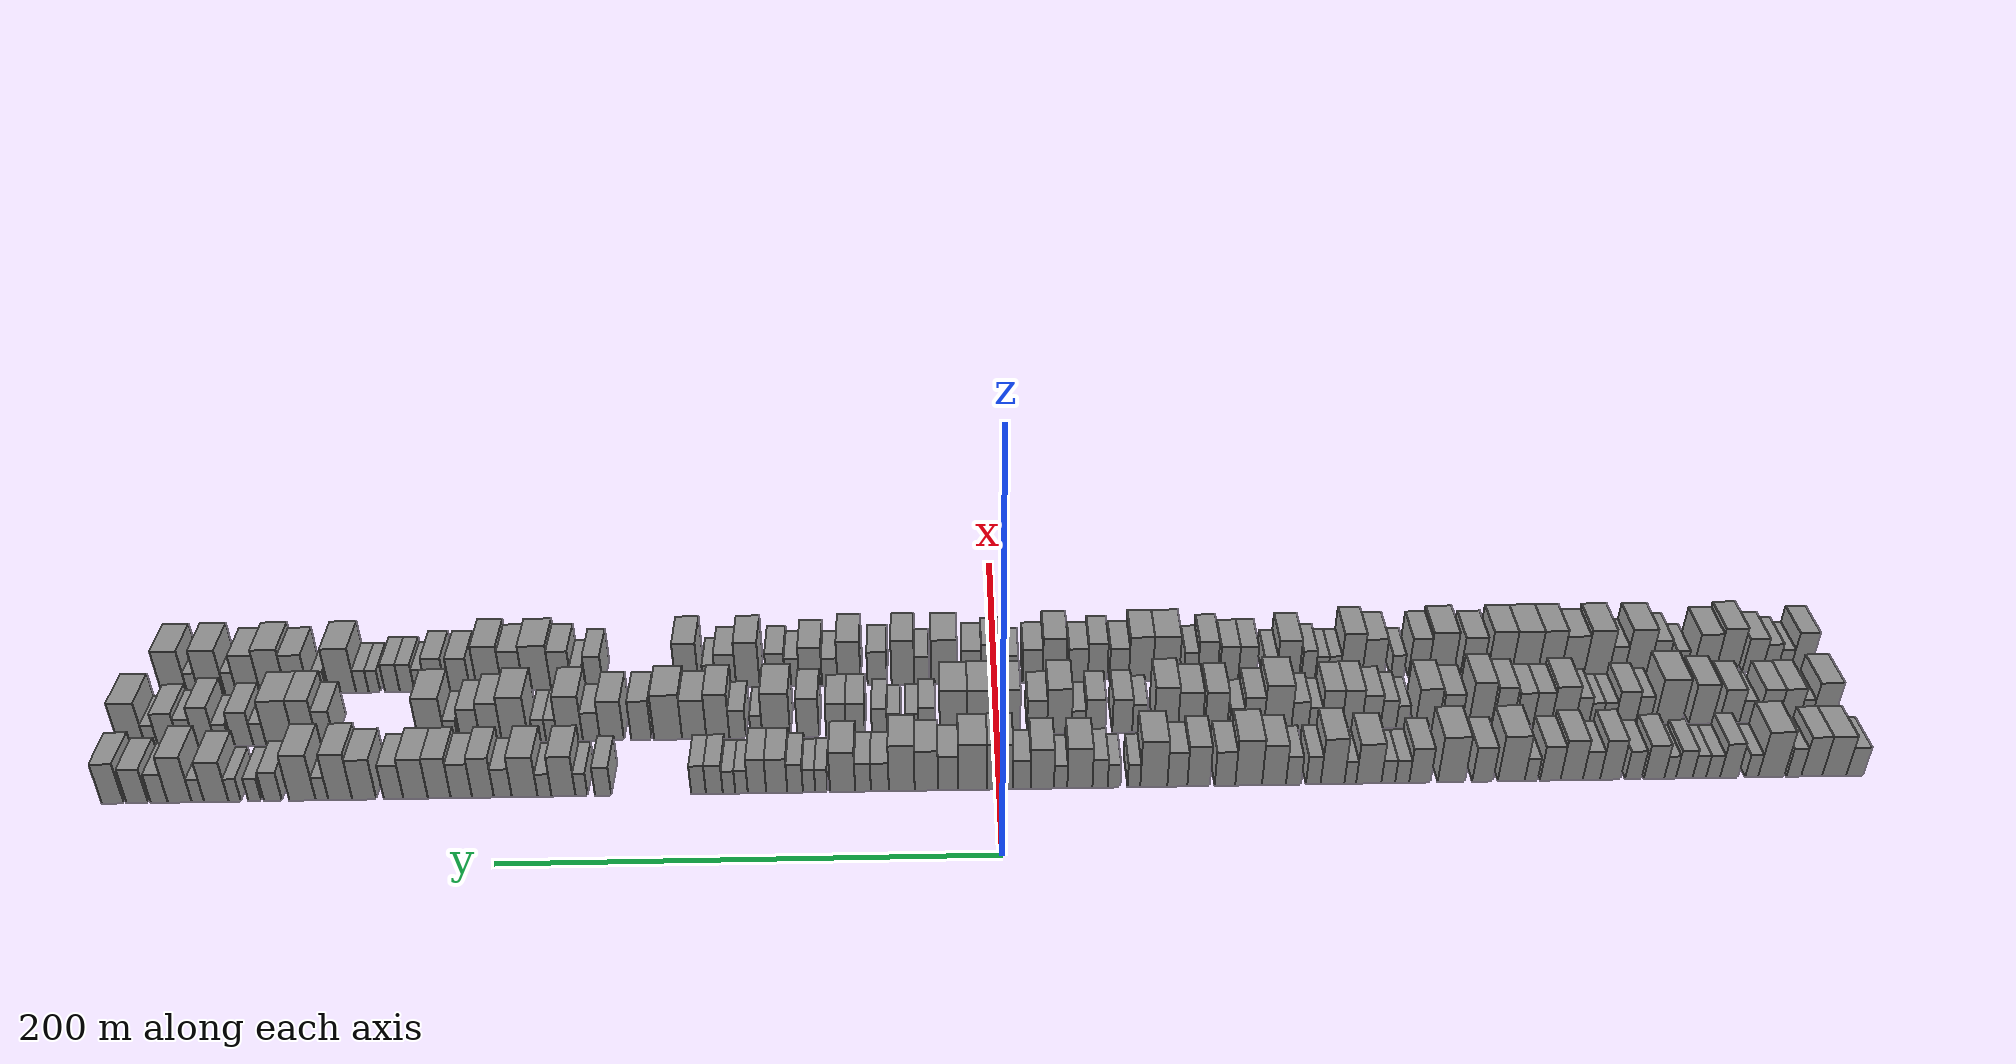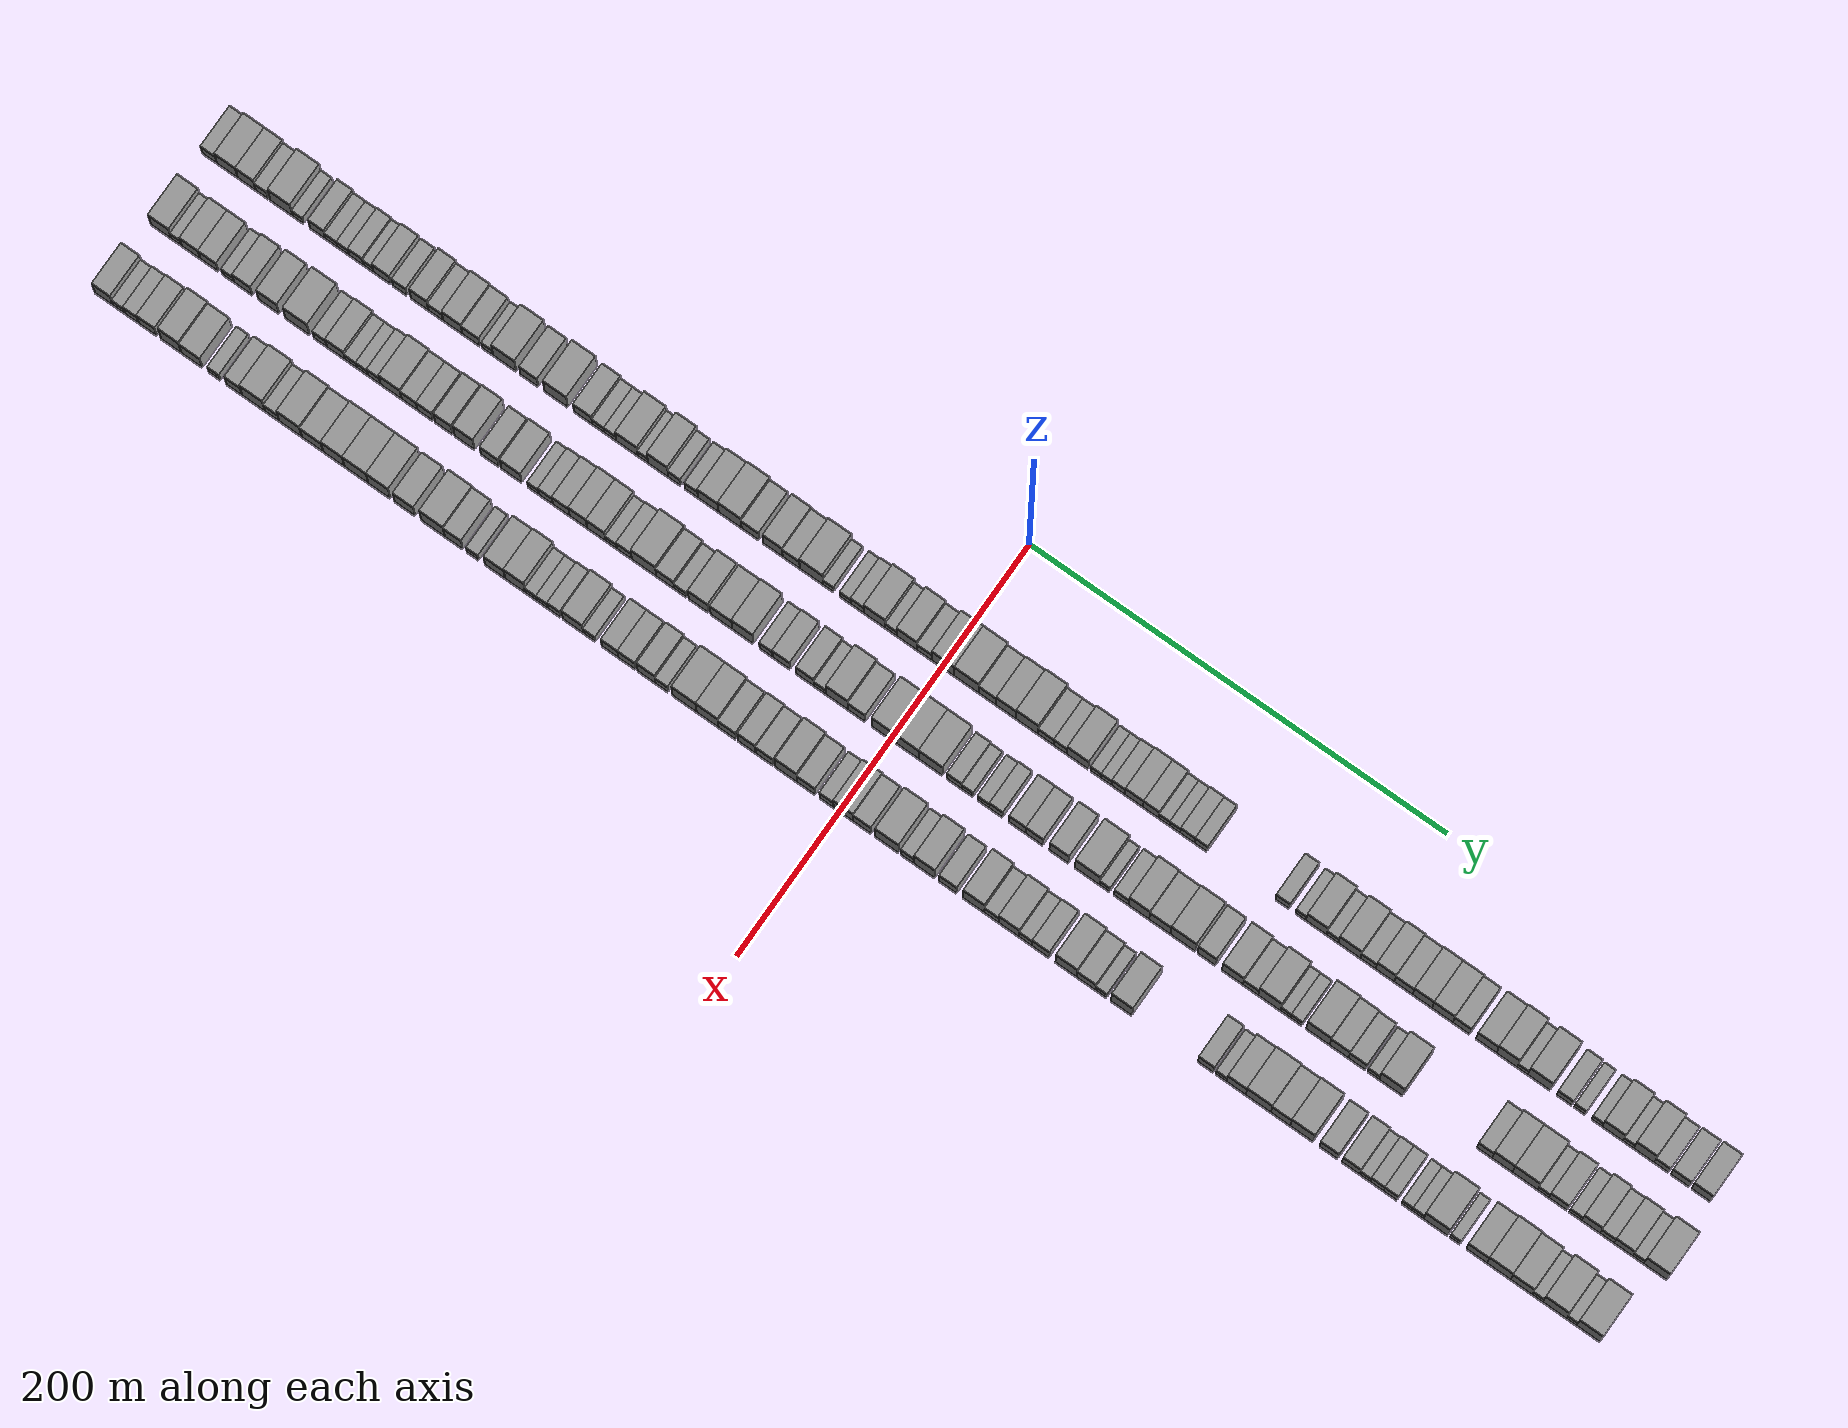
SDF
<sdf version="1.6">
 <world name="default">
  <scene>
   <sky><clouds><speed>12</speed></clouds></sky>
   <ambient>0.4 0.4 0.4 1</ambient>
   <background>0.7 0.7 0.7 1</background>
   <shadows>1</shadows>
  </scene>
  <gravity>0 0 -9.8066</gravity>
  <magnetic_field>6e-06 2.3e-05 -4.2e-05</magnetic_field>
  <physics default="0" name="default_physics" type="ode">
   <ode>
    <solver>
     <type>quick</type>
     <iters>10</iters>
     <sor>1.0</sor>
     <use_dynamic_moi_rescaling>0</use_dynamic_moi_rescaling>
    </solver>
    <constraints>
     <cfm>0</cfm>
     <erp>0.2</erp>
     <contact_max_correcting_vel>100</contact_max_correcting_vel>
     <contact_surface_layer>0.001</contact_surface_layer>
    </constraints>
   </ode>
   <max_step_size>0.004</max_step_size>
   <real_time_factor>1</real_time_factor>
   <real_time_update_rate>250</real_time_update_rate>
  </physics>
  <light name="sun" type="directional">
   <pose>0 0 10 0 0 0</pose>
   <diffuse>0.8 0.8 0.8 1</diffuse>
   <specular>0.2 0.2 0.2 1</specular>
   <attenuation>
    <range>1000</range>
    <constant>0.9</constant>
    <linear>0.01</linear>
    <quadratic>0.001</quadratic>
   </attenuation>
   <direction>-0.5 0.1 -0.9</direction>
  </light>
  <model name="building_1">
   <static>1</static>
   <pose>50.0000 -354.4526 0 0.000000 0.000000 0.000000</pose>
   <link name="link">
    <pose>0 0 7.50 0 0 0</pose>
    <collision name="collision"><geometry><box><size>20.0000 7.0948 15.0000</size></box></geometry></collision>
    <visual name="visual">
     <cast_shadows>0</cast_shadows>
     <geometry><box><size>20.0000 7.0948 15.0000</size></box></geometry>
     <material>
      <script>
       <uri>model://grey_wall/materials/scripts</uri>
       <uri>model://grey_wall/materials/textures</uri>
       <name>vrc/grey_wall</name>
      </script>
     </material>
    </visual>
   </link>
  </model>
  <model name="building_2">
   <static>1</static>
   <pose>50.0000 -345.8358 0 0.000000 0.000000 0.000000</pose>
   <link name="link">
    <pose>0 0 10.50 0 0 0</pose>
    <collision name="collision"><geometry><box><size>20.0000 10.1390 21.0000</size></box></geometry></collision>
    <visual name="visual">
     <cast_shadows>0</cast_shadows>
     <geometry><box><size>20.0000 10.1390 21.0000</size></box></geometry>
     <material>
      <script>
       <uri>model://grey_wall/materials/scripts</uri>
       <uri>model://grey_wall/materials/textures</uri>
       <name>vrc/grey_wall</name>
      </script>
     </material>
    </visual>
   </link>
  </model>
  <model name="building_3">
   <static>1</static>
   <pose>50.0000 -336.3879 0 0.000000 0.000000 0.000000</pose>
   <link name="link">
    <pose>0 0 10.50 0 0 0</pose>
    <collision name="collision"><geometry><box><size>20.0000 8.7568 21.0000</size></box></geometry></collision>
    <visual name="visual">
     <cast_shadows>0</cast_shadows>
     <geometry><box><size>20.0000 8.7568 21.0000</size></box></geometry>
     <material>
      <script>
       <uri>model://grey_wall/materials/scripts</uri>
       <uri>model://grey_wall/materials/textures</uri>
       <name>vrc/grey_wall</name>
      </script>
     </material>
    </visual>
   </link>
  </model>
  <model name="building_4">
   <static>1</static>
   <pose>50.0000 -328.9606 0 0.000000 0.000000 0.000000</pose>
   <link name="link">
    <pose>0 0 7.50 0 0 0</pose>
    <collision name="collision"><geometry><box><size>20.0000 6.0978 15.0000</size></box></geometry></collision>
    <visual name="visual">
     <cast_shadows>0</cast_shadows>
     <geometry><box><size>20.0000 6.0978 15.0000</size></box></geometry>
     <material>
      <script>
       <uri>model://grey_wall/materials/scripts</uri>
       <uri>model://grey_wall/materials/textures</uri>
       <name>vrc/grey_wall</name>
      </script>
     </material>
    </visual>
   </link>
  </model>
  <model name="building_5">
   <static>1</static>
   <pose>50.0000 -319.4855 0 0.000000 0.000000 0.000000</pose>
   <link name="link">
    <pose>0 0 12.00 0 0 0</pose>
    <collision name="collision"><geometry><box><size>20.0000 10.8523 24.0000</size></box></geometry></collision>
    <visual name="visual">
     <cast_shadows>0</cast_shadows>
     <geometry><box><size>20.0000 10.8523 24.0000</size></box></geometry>
     <material>
      <script>
       <uri>model://grey_wall/materials/scripts</uri>
       <uri>model://grey_wall/materials/textures</uri>
       <name>vrc/grey_wall</name>
      </script>
     </material>
    </visual>
   </link>
  </model>
  <model name="building_6">
   <static>1</static>
   <pose>50.0000 -311.3605 0 0.000000 0.000000 0.000000</pose>
   <link name="link">
    <pose>0 0 6.00 0 0 0</pose>
    <collision name="collision"><geometry><box><size>20.0000 5.3977 12.0000</size></box></geometry></collision>
    <visual name="visual">
     <cast_shadows>0</cast_shadows>
     <geometry><box><size>20.0000 5.3977 12.0000</size></box></geometry>
     <material>
      <script>
       <uri>model://grey_wall/materials/scripts</uri>
       <uri>model://grey_wall/materials/textures</uri>
       <name>vrc/grey_wall</name>
      </script>
     </material>
    </visual>
   </link>
  </model>
  <model name="building_7">
   <static>1</static>
   <pose>50.0000 -301.9063 0 0.000000 0.000000 0.000000</pose>
   <link name="link">
    <pose>0 0 9.00 0 0 0</pose>
    <collision name="collision"><geometry><box><size>20.0000 7.5106 18.0000</size></box></geometry></collision>
    <visual name="visual">
     <cast_shadows>0</cast_shadows>
     <geometry><box><size>20.0000 7.5106 18.0000</size></box></geometry>
     <material>
      <script>
       <uri>model://grey_wall/materials/scripts</uri>
       <uri>model://grey_wall/materials/textures</uri>
       <name>vrc/grey_wall</name>
      </script>
     </material>
    </visual>
   </link>
  </model>
  <model name="building_8">
   <static>1</static>
   <pose>50.0000 -295.2323 0 0.000000 0.000000 0.000000</pose>
   <link name="link">
    <pose>0 0 6.00 0 0 0</pose>
    <collision name="collision"><geometry><box><size>20.0000 5.8375 12.0000</size></box></geometry></collision>
    <visual name="visual">
     <cast_shadows>0</cast_shadows>
     <geometry><box><size>20.0000 5.8375 12.0000</size></box></geometry>
     <material>
      <script>
       <uri>model://grey_wall/materials/scripts</uri>
       <uri>model://grey_wall/materials/textures</uri>
       <name>vrc/grey_wall</name>
      </script>
     </material>
    </visual>
   </link>
  </model>
  <model name="building_9">
   <static>1</static>
   <pose>50.0000 -289.4980 0 0.000000 0.000000 0.000000</pose>
   <link name="link">
    <pose>0 0 6.00 0 0 0</pose>
    <collision name="collision"><geometry><box><size>20.0000 5.6311 12.0000</size></box></geometry></collision>
    <visual name="visual">
     <cast_shadows>0</cast_shadows>
     <geometry><box><size>20.0000 5.6311 12.0000</size></box></geometry>
     <material>
      <script>
       <uri>model://grey_wall/materials/scripts</uri>
       <uri>model://grey_wall/materials/textures</uri>
       <name>vrc/grey_wall</name>
      </script>
     </material>
    </visual>
   </link>
  </model>
  <model name="building_10">
   <static>1</static>
   <pose>50.0000 -283.2031 0 0.000000 0.000000 0.000000</pose>
   <link name="link">
    <pose>0 0 7.50 0 0 0</pose>
    <collision name="collision"><geometry><box><size>20.0000 6.9587 15.0000</size></box></geometry></collision>
    <visual name="visual">
     <cast_shadows>0</cast_shadows>
     <geometry><box><size>20.0000 6.9587 15.0000</size></box></geometry>
     <material>
      <script>
       <uri>model://grey_wall/materials/scripts</uri>
       <uri>model://grey_wall/materials/textures</uri>
       <name>vrc/grey_wall</name>
      </script>
     </material>
    </visual>
   </link>
  </model>
  <model name="building_11">
   <static>1</static>
   <pose>50.0000 -277.3180 0 0.000000 0.000000 0.000000</pose>
   <link name="link">
    <pose>0 0 6.00 0 0 0</pose>
    <collision name="collision"><geometry><box><size>20.0000 4.8116 12.0000</size></box></geometry></collision>
    <visual name="visual">
     <cast_shadows>0</cast_shadows>
     <geometry><box><size>20.0000 4.8116 12.0000</size></box></geometry>
     <material>
      <script>
       <uri>model://grey_wall/materials/scripts</uri>
       <uri>model://grey_wall/materials/textures</uri>
       <name>vrc/grey_wall</name>
      </script>
     </material>
    </visual>
   </link>
  </model>
  <model name="building_12">
   <static>1</static>
   <pose>50.0000 -270.6634 0 0.000000 0.000000 0.000000</pose>
   <link name="link">
    <pose>0 0 9.00 0 0 0</pose>
    <collision name="collision"><geometry><box><size>20.0000 8.4977 18.0000</size></box></geometry></collision>
    <visual name="visual">
     <cast_shadows>0</cast_shadows>
     <geometry><box><size>20.0000 8.4977 18.0000</size></box></geometry>
     <material>
      <script>
       <uri>model://grey_wall/materials/scripts</uri>
       <uri>model://grey_wall/materials/textures</uri>
       <name>vrc/grey_wall</name>
      </script>
     </material>
    </visual>
   </link>
  </model>
  <model name="building_13">
   <static>1</static>
   <pose>50.0000 -262.0144 0 0.000000 0.000000 0.000000</pose>
   <link name="link">
    <pose>0 0 7.50 0 0 0</pose>
    <collision name="collision"><geometry><box><size>20.0000 6.8003 15.0000</size></box></geometry></collision>
    <visual name="visual">
     <cast_shadows>0</cast_shadows>
     <geometry><box><size>20.0000 6.8003 15.0000</size></box></geometry>
     <material>
      <script>
       <uri>model://grey_wall/materials/scripts</uri>
       <uri>model://grey_wall/materials/textures</uri>
       <name>vrc/grey_wall</name>
      </script>
     </material>
    </visual>
   </link>
  </model>
  <model name="building_14">
   <static>1</static>
   <pose>50.0000 -252.3882 0 0.000000 0.000000 0.000000</pose>
   <link name="link">
    <pose>0 0 10.50 0 0 0</pose>
    <collision name="collision"><geometry><box><size>20.0000 8.4520 21.0000</size></box></geometry></collision>
    <visual name="visual">
     <cast_shadows>0</cast_shadows>
     <geometry><box><size>20.0000 8.4520 21.0000</size></box></geometry>
     <material>
      <script>
       <uri>model://grey_wall/materials/scripts</uri>
       <uri>model://grey_wall/materials/textures</uri>
       <name>vrc/grey_wall</name>
      </script>
     </material>
    </visual>
   </link>
  </model>
  <model name="building_15">
   <static>1</static>
   <pose>50.0000 -244.5820 0 0.000000 0.000000 0.000000</pose>
   <link name="link">
    <pose>0 0 7.50 0 0 0</pose>
    <collision name="collision"><geometry><box><size>20.0000 7.1606 15.0000</size></box></geometry></collision>
    <visual name="visual">
     <cast_shadows>0</cast_shadows>
     <geometry><box><size>20.0000 7.1606 15.0000</size></box></geometry>
     <material>
      <script>
       <uri>model://grey_wall/materials/scripts</uri>
       <uri>model://grey_wall/materials/textures</uri>
       <name>vrc/grey_wall</name>
      </script>
     </material>
    </visual>
   </link>
  </model>
  <model name="building_16">
   <static>1</static>
   <pose>50.0000 -236.3634 0 0.000000 0.000000 0.000000</pose>
   <link name="link">
    <pose>0 0 10.50 0 0 0</pose>
    <collision name="collision"><geometry><box><size>20.0000 9.2764 21.0000</size></box></geometry></collision>
    <visual name="visual">
     <cast_shadows>0</cast_shadows>
     <geometry><box><size>20.0000 9.2764 21.0000</size></box></geometry>
     <material>
      <script>
       <uri>model://grey_wall/materials/scripts</uri>
       <uri>model://grey_wall/materials/textures</uri>
       <name>vrc/grey_wall</name>
      </script>
     </material>
    </visual>
   </link>
  </model>
  <model name="building_17">
   <static>1</static>
   <pose>50.0000 -227.4491 0 0.000000 0.000000 0.000000</pose>
   <link name="link">
    <pose>0 0 9.00 0 0 0</pose>
    <collision name="collision"><geometry><box><size>20.0000 8.5524 18.0000</size></box></geometry></collision>
    <visual name="visual">
     <cast_shadows>0</cast_shadows>
     <geometry><box><size>20.0000 8.5524 18.0000</size></box></geometry>
     <material>
      <script>
       <uri>model://grey_wall/materials/scripts</uri>
       <uri>model://grey_wall/materials/textures</uri>
       <name>vrc/grey_wall</name>
      </script>
     </material>
    </visual>
   </link>
  </model>
  <model name="building_18">
   <static>1</static>
   <pose>50.0000 -219.5066 0 0.000000 0.000000 0.000000</pose>
   <link name="link">
    <pose>0 0 6.00 0 0 0</pose>
    <collision name="collision"><geometry><box><size>20.0000 5.3324 12.0000</size></box></geometry></collision>
    <visual name="visual">
     <cast_shadows>0</cast_shadows>
     <geometry><box><size>20.0000 5.3324 12.0000</size></box></geometry>
     <material>
      <script>
       <uri>model://grey_wall/materials/scripts</uri>
       <uri>model://grey_wall/materials/textures</uri>
       <name>vrc/grey_wall</name>
      </script>
     </material>
    </visual>
   </link>
  </model>
  <model name="building_19">
   <static>1</static>
   <pose>50.0000 -211.2568 0 0.000000 0.000000 0.000000</pose>
   <link name="link">
    <pose>0 0 12.00 0 0 0</pose>
    <collision name="collision"><geometry><box><size>20.0000 11.1674 24.0000</size></box></geometry></collision>
    <visual name="visual">
     <cast_shadows>0</cast_shadows>
     <geometry><box><size>20.0000 11.1674 24.0000</size></box></geometry>
     <material>
      <script>
       <uri>model://grey_wall/materials/scripts</uri>
       <uri>model://grey_wall/materials/textures</uri>
       <name>vrc/grey_wall</name>
      </script>
     </material>
    </visual>
   </link>
  </model>
  <model name="building_20">
   <static>1</static>
   <pose>50.0000 -199.3447 0 0.000000 0.000000 0.000000</pose>
   <link name="link">
    <pose>0 0 9.00 0 0 0</pose>
    <collision name="collision"><geometry><box><size>20.0000 8.6568 18.0000</size></box></geometry></collision>
    <visual name="visual">
     <cast_shadows>0</cast_shadows>
     <geometry><box><size>20.0000 8.6568 18.0000</size></box></geometry>
     <material>
      <script>
       <uri>model://grey_wall/materials/scripts</uri>
       <uri>model://grey_wall/materials/textures</uri>
       <name>vrc/grey_wall</name>
      </script>
     </material>
    </visual>
   </link>
  </model>
  <model name="building_21">
   <static>1</static>
   <pose>50.0000 -186.3479 0 0.000000 0.000000 0.000000</pose>
   <link name="link">
    <pose>0 0 12.00 0 0 0</pose>
    <collision name="collision"><geometry><box><size>20.0000 11.3366 24.0000</size></box></geometry></collision>
    <visual name="visual">
     <cast_shadows>0</cast_shadows>
     <geometry><box><size>20.0000 11.3366 24.0000</size></box></geometry>
     <material>
      <script>
       <uri>model://grey_wall/materials/scripts</uri>
       <uri>model://grey_wall/materials/textures</uri>
       <name>vrc/grey_wall</name>
      </script>
     </material>
    </visual>
   </link>
  </model>
  <model name="building_22">
   <static>1</static>
   <pose>50.0000 -173.2719 0 0.000000 0.000000 0.000000</pose>
   <link name="link">
    <pose>0 0 9.00 0 0 0</pose>
    <collision name="collision"><geometry><box><size>20.0000 8.8156 18.0000</size></box></geometry></collision>
    <visual name="visual">
     <cast_shadows>0</cast_shadows>
     <geometry><box><size>20.0000 8.8156 18.0000</size></box></geometry>
     <material>
      <script>
       <uri>model://grey_wall/materials/scripts</uri>
       <uri>model://grey_wall/materials/textures</uri>
       <name>vrc/grey_wall</name>
      </script>
     </material>
    </visual>
   </link>
  </model>
  <model name="building_23">
   <static>1</static>
   <pose>50.0000 -165.9495 0 0.000000 0.000000 0.000000</pose>
   <link name="link">
    <pose>0 0 6.00 0 0 0</pose>
    <collision name="collision"><geometry><box><size>20.0000 5.8291 12.0000</size></box></geometry></collision>
    <visual name="visual">
     <cast_shadows>0</cast_shadows>
     <geometry><box><size>20.0000 5.8291 12.0000</size></box></geometry>
     <material>
      <script>
       <uri>model://grey_wall/materials/scripts</uri>
       <uri>model://grey_wall/materials/textures</uri>
       <name>vrc/grey_wall</name>
      </script>
     </material>
    </visual>
   </link>
  </model>
  <model name="building_24">
   <static>1</static>
   <pose>50.0000 -160.1838 0 0.000000 0.000000 0.000000</pose>
   <link name="link">
    <pose>0 0 6.00 0 0 0</pose>
    <collision name="collision"><geometry><box><size>20.0000 5.7024 12.0000</size></box></geometry></collision>
    <visual name="visual">
     <cast_shadows>0</cast_shadows>
     <geometry><box><size>20.0000 5.7024 12.0000</size></box></geometry>
     <material>
      <script>
       <uri>model://grey_wall/materials/scripts</uri>
       <uri>model://grey_wall/materials/textures</uri>
       <name>vrc/grey_wall</name>
      </script>
     </material>
    </visual>
   </link>
  </model>
  <model name="building_25">
   <static>1</static>
   <pose>50.0000 -152.0896 0 0.000000 0.000000 0.000000</pose>
   <link name="link">
    <pose>0 0 10.50 0 0 0</pose>
    <collision name="collision"><geometry><box><size>20.0000 10.4859 21.0000</size></box></geometry></collision>
    <visual name="visual">
     <cast_shadows>0</cast_shadows>
     <geometry><box><size>20.0000 10.4859 21.0000</size></box></geometry>
     <material>
      <script>
       <uri>model://grey_wall/materials/scripts</uri>
       <uri>model://grey_wall/materials/textures</uri>
       <name>vrc/grey_wall</name>
      </script>
     </material>
    </visual>
   </link>
  </model>
  <model name="building_26">
   <static>1</static>
   <pose>50.0000 -144.4280 0 0.000000 0.000000 0.000000</pose>
   <link name="link">
    <pose>0 0 6.00 0 0 0</pose>
    <collision name="collision"><geometry><box><size>20.0000 4.8373 12.0000</size></box></geometry></collision>
    <visual name="visual">
     <cast_shadows>0</cast_shadows>
     <geometry><box><size>20.0000 4.8373 12.0000</size></box></geometry>
     <material>
      <script>
       <uri>model://grey_wall/materials/scripts</uri>
       <uri>model://grey_wall/materials/textures</uri>
       <name>vrc/grey_wall</name>
      </script>
     </material>
    </visual>
   </link>
  </model>
  <model name="building_27">
   <static>1</static>
   <pose>50.0000 -137.0855 0 0.000000 0.000000 0.000000</pose>
   <link name="link">
    <pose>0 0 12.00 0 0 0</pose>
    <collision name="collision"><geometry><box><size>20.0000 9.8476 24.0000</size></box></geometry></collision>
    <visual name="visual">
     <cast_shadows>0</cast_shadows>
     <geometry><box><size>20.0000 9.8476 24.0000</size></box></geometry>
     <material>
      <script>
       <uri>model://grey_wall/materials/scripts</uri>
       <uri>model://grey_wall/materials/textures</uri>
       <name>vrc/grey_wall</name>
      </script>
     </material>
    </visual>
   </link>
  </model>
  <model name="building_28">
   <static>1</static>
   <pose>50.0000 -129.1241 0 0.000000 0.000000 0.000000</pose>
   <link name="link">
    <pose>0 0 7.50 0 0 0</pose>
    <collision name="collision"><geometry><box><size>20.0000 6.0752 15.0000</size></box></geometry></collision>
    <visual name="visual">
     <cast_shadows>0</cast_shadows>
     <geometry><box><size>20.0000 6.0752 15.0000</size></box></geometry>
     <material>
      <script>
       <uri>model://grey_wall/materials/scripts</uri>
       <uri>model://grey_wall/materials/textures</uri>
       <name>vrc/grey_wall</name>
      </script>
     </material>
    </visual>
   </link>
  </model>
  <model name="building_29">
   <static>1</static>
   <pose>50.0000 -120.9508 0 0.000000 0.000000 0.000000</pose>
   <link name="link">
    <pose>0 0 7.50 0 0 0</pose>
    <collision name="collision"><geometry><box><size>20.0000 6.2715 15.0000</size></box></geometry></collision>
    <visual name="visual">
     <cast_shadows>0</cast_shadows>
     <geometry><box><size>20.0000 6.2715 15.0000</size></box></geometry>
     <material>
      <script>
       <uri>model://grey_wall/materials/scripts</uri>
       <uri>model://grey_wall/materials/textures</uri>
       <name>vrc/grey_wall</name>
      </script>
     </material>
    </visual>
   </link>
  </model>
  <model name="building_30">
   <static>1</static>
   <pose>50.0000 -112.8564 0 0.000000 0.000000 0.000000</pose>
   <link name="link">
    <pose>0 0 10.50 0 0 0</pose>
    <collision name="collision"><geometry><box><size>20.0000 9.9175 21.0000</size></box></geometry></collision>
    <visual name="visual">
     <cast_shadows>0</cast_shadows>
     <geometry><box><size>20.0000 9.9175 21.0000</size></box></geometry>
     <material>
      <script>
       <uri>model://grey_wall/materials/scripts</uri>
       <uri>model://grey_wall/materials/textures</uri>
       <name>vrc/grey_wall</name>
      </script>
     </material>
    </visual>
   </link>
  </model>
  <model name="building_31">
   <static>1</static>
   <pose>50.0000 -102.3716 0 0.000000 0.000000 0.000000</pose>
   <link name="link">
    <pose>0 0 12.00 0 0 0</pose>
    <collision name="collision"><geometry><box><size>20.0000 11.0521 24.0000</size></box></geometry></collision>
    <visual name="visual">
     <cast_shadows>0</cast_shadows>
     <geometry><box><size>20.0000 11.0521 24.0000</size></box></geometry>
     <material>
      <script>
       <uri>model://grey_wall/materials/scripts</uri>
       <uri>model://grey_wall/materials/textures</uri>
       <name>vrc/grey_wall</name>
      </script>
     </material>
    </visual>
   </link>
  </model>
  <model name="building_32">
   <static>1</static>
   <pose>50.0000 -92.6027 0 0.000000 0.000000 0.000000</pose>
   <link name="link">
    <pose>0 0 9.00 0 0 0</pose>
    <collision name="collision"><geometry><box><size>20.0000 8.4857 18.0000</size></box></geometry></collision>
    <visual name="visual">
     <cast_shadows>0</cast_shadows>
     <geometry><box><size>20.0000 8.4857 18.0000</size></box></geometry>
     <material>
      <script>
       <uri>model://grey_wall/materials/scripts</uri>
       <uri>model://grey_wall/materials/textures</uri>
       <name>vrc/grey_wall</name>
      </script>
     </material>
    </visual>
   </link>
  </model>
  <model name="building_33">
   <static>1</static>
   <pose>50.0000 -81.7092 0 0.000000 0.000000 0.000000</pose>
   <link name="link">
    <pose>0 0 10.50 0 0 0</pose>
    <collision name="collision"><geometry><box><size>20.0000 9.3013 21.0000</size></box></geometry></collision>
    <visual name="visual">
     <cast_shadows>0</cast_shadows>
     <geometry><box><size>20.0000 9.3013 21.0000</size></box></geometry>
     <material>
      <script>
       <uri>model://grey_wall/materials/scripts</uri>
       <uri>model://grey_wall/materials/textures</uri>
       <name>vrc/grey_wall</name>
      </script>
     </material>
    </visual>
   </link>
  </model>
  <model name="building_34">
   <static>1</static>
   <pose>50.0000 -72.9314 0 0.000000 0.000000 0.000000</pose>
   <link name="link">
    <pose>0 0 9.00 0 0 0</pose>
    <collision name="collision"><geometry><box><size>20.0000 8.2544 18.0000</size></box></geometry></collision>
    <visual name="visual">
     <cast_shadows>0</cast_shadows>
     <geometry><box><size>20.0000 8.2544 18.0000</size></box></geometry>
     <material>
      <script>
       <uri>model://grey_wall/materials/scripts</uri>
       <uri>model://grey_wall/materials/textures</uri>
       <name>vrc/grey_wall</name>
      </script>
     </material>
    </visual>
   </link>
  </model>
  <model name="building_35">
   <static>1</static>
   <pose>50.0000 -63.2243 0 0.000000 0.000000 0.000000</pose>
   <link name="link">
    <pose>0 0 12.00 0 0 0</pose>
    <collision name="collision"><geometry><box><size>20.0000 11.1598 24.0000</size></box></geometry></collision>
    <visual name="visual">
     <cast_shadows>0</cast_shadows>
     <geometry><box><size>20.0000 11.1598 24.0000</size></box></geometry>
     <material>
      <script>
       <uri>model://grey_wall/materials/scripts</uri>
       <uri>model://grey_wall/materials/textures</uri>
       <name>vrc/grey_wall</name>
      </script>
     </material>
    </visual>
   </link>
  </model>
  <model name="building_36">
   <static>1</static>
   <pose>50.0000 -55.0283 0 0.000000 0.000000 0.000000</pose>
   <link name="link">
    <pose>0 0 6.00 0 0 0</pose>
    <collision name="collision"><geometry><box><size>20.0000 5.2321 12.0000</size></box></geometry></collision>
    <visual name="visual">
     <cast_shadows>0</cast_shadows>
     <geometry><box><size>20.0000 5.2321 12.0000</size></box></geometry>
     <material>
      <script>
       <uri>model://grey_wall/materials/scripts</uri>
       <uri>model://grey_wall/materials/textures</uri>
       <name>vrc/grey_wall</name>
      </script>
     </material>
    </visual>
   </link>
  </model>
  <model name="building_37">
   <static>1</static>
   <pose>50.0000 -46.8192 0 0.000000 0.000000 0.000000</pose>
   <link name="link">
    <pose>0 0 6.00 0 0 0</pose>
    <collision name="collision"><geometry><box><size>20.0000 5.1861 12.0000</size></box></geometry></collision>
    <visual name="visual">
     <cast_shadows>0</cast_shadows>
     <geometry><box><size>20.0000 5.1861 12.0000</size></box></geometry>
     <material>
      <script>
       <uri>model://grey_wall/materials/scripts</uri>
       <uri>model://grey_wall/materials/textures</uri>
       <name>vrc/grey_wall</name>
      </script>
     </material>
    </visual>
   </link>
  </model>
  <model name="building_38">
   <static>1</static>
   <pose>50.0000 -41.0748 0 0.000000 0.000000 0.000000</pose>
   <link name="link">
    <pose>0 0 7.50 0 0 0</pose>
    <collision name="collision"><geometry><box><size>20.0000 6.3028 15.0000</size></box></geometry></collision>
    <visual name="visual">
     <cast_shadows>0</cast_shadows>
     <geometry><box><size>20.0000 6.3028 15.0000</size></box></geometry>
     <material>
      <script>
       <uri>model://grey_wall/materials/scripts</uri>
       <uri>model://grey_wall/materials/textures</uri>
       <name>vrc/grey_wall</name>
      </script>
     </material>
    </visual>
   </link>
  </model>
  <model name="building_39">
   <static>1</static>
   <pose>50.0000 -32.7464 0 0.000000 0.000000 0.000000</pose>
   <link name="link">
    <pose>0 0 10.50 0 0 0</pose>
    <collision name="collision"><geometry><box><size>20.0000 10.3540 21.0000</size></box></geometry></collision>
    <visual name="visual">
     <cast_shadows>0</cast_shadows>
     <geometry><box><size>20.0000 10.3540 21.0000</size></box></geometry>
     <material>
      <script>
       <uri>model://grey_wall/materials/scripts</uri>
       <uri>model://grey_wall/materials/textures</uri>
       <name>vrc/grey_wall</name>
      </script>
     </material>
    </visual>
   </link>
  </model>
  <model name="building_40">
   <static>1</static>
   <pose>50.0000 -24.8430 0 0.000000 0.000000 0.000000</pose>
   <link name="link">
    <pose>0 0 6.00 0 0 0</pose>
    <collision name="collision"><geometry><box><size>20.0000 5.4528 12.0000</size></box></geometry></collision>
    <visual name="visual">
     <cast_shadows>0</cast_shadows>
     <geometry><box><size>20.0000 5.4528 12.0000</size></box></geometry>
     <material>
      <script>
       <uri>model://grey_wall/materials/scripts</uri>
       <uri>model://grey_wall/materials/textures</uri>
       <name>vrc/grey_wall</name>
      </script>
     </material>
    </visual>
   </link>
  </model>
  <model name="building_41">
   <static>1</static>
   <pose>50.0000 -17.2844 0 0.000000 0.000000 0.000000</pose>
   <link name="link">
    <pose>0 0 10.50 0 0 0</pose>
    <collision name="collision"><geometry><box><size>20.0000 9.6644 21.0000</size></box></geometry></collision>
    <visual name="visual">
     <cast_shadows>0</cast_shadows>
     <geometry><box><size>20.0000 9.6644 21.0000</size></box></geometry>
     <material>
      <script>
       <uri>model://grey_wall/materials/scripts</uri>
       <uri>model://grey_wall/materials/textures</uri>
       <name>vrc/grey_wall</name>
      </script>
     </material>
    </visual>
   </link>
  </model>
  <model name="building_42">
   <static>1</static>
   <pose>50.0000 -8.8201 0 0.000000 0.000000 0.000000</pose>
   <link name="link">
    <pose>0 0 7.50 0 0 0</pose>
    <collision name="collision"><geometry><box><size>20.0000 7.2641 15.0000</size></box></geometry></collision>
    <visual name="visual">
     <cast_shadows>0</cast_shadows>
     <geometry><box><size>20.0000 7.2641 15.0000</size></box></geometry>
     <material>
      <script>
       <uri>model://grey_wall/materials/scripts</uri>
       <uri>model://grey_wall/materials/textures</uri>
       <name>vrc/grey_wall</name>
      </script>
     </material>
    </visual>
   </link>
  </model>
  <model name="building_43">
   <static>1</static>
   <pose>50.0000 0.1248 0 0.000000 0.000000 0.000000</pose>
   <link name="link">
    <pose>0 0 12.00 0 0 0</pose>
    <collision name="collision"><geometry><box><size>20.0000 10.6258 24.0000</size></box></geometry></collision>
    <visual name="visual">
     <cast_shadows>0</cast_shadows>
     <geometry><box><size>20.0000 10.6258 24.0000</size></box></geometry>
     <material>
      <script>
       <uri>model://grey_wall/materials/scripts</uri>
       <uri>model://grey_wall/materials/textures</uri>
       <name>vrc/grey_wall</name>
      </script>
     </material>
    </visual>
   </link>
  </model>
  <model name="building_44">
   <static>1</static>
   <pose>50.0000 11.3417 0 0.000000 0.000000 0.000000</pose>
   <link name="link">
    <pose>0 0 12.00 0 0 0</pose>
    <collision name="collision"><geometry><box><size>20.0000 11.8079 24.0000</size></box></geometry></collision>
    <visual name="visual">
     <cast_shadows>0</cast_shadows>
     <geometry><box><size>20.0000 11.8079 24.0000</size></box></geometry>
     <material>
      <script>
       <uri>model://grey_wall/materials/scripts</uri>
       <uri>model://grey_wall/materials/textures</uri>
       <name>vrc/grey_wall</name>
      </script>
     </material>
    </visual>
   </link>
  </model>
  <model name="building_45">
   <static>1</static>
   <pose>50.0000 21.4188 0 0.000000 0.000000 0.000000</pose>
   <link name="link">
    <pose>0 0 9.00 0 0 0</pose>
    <collision name="collision"><geometry><box><size>20.0000 8.3464 18.0000</size></box></geometry></collision>
    <visual name="visual">
     <cast_shadows>0</cast_shadows>
     <geometry><box><size>20.0000 8.3464 18.0000</size></box></geometry>
     <material>
      <script>
       <uri>model://grey_wall/materials/scripts</uri>
       <uri>model://grey_wall/materials/textures</uri>
       <name>vrc/grey_wall</name>
      </script>
     </material>
    </visual>
   </link>
  </model>
  <model name="building_46">
   <static>1</static>
   <pose>50.0000 30.3973 0 0.000000 0.000000 0.000000</pose>
   <link name="link">
    <pose>0 0 10.50 0 0 0</pose>
    <collision name="collision"><geometry><box><size>20.0000 9.6105 21.0000</size></box></geometry></collision>
    <visual name="visual">
     <cast_shadows>0</cast_shadows>
     <geometry><box><size>20.0000 9.6105 21.0000</size></box></geometry>
     <material>
      <script>
       <uri>model://grey_wall/materials/scripts</uri>
       <uri>model://grey_wall/materials/textures</uri>
       <name>vrc/grey_wall</name>
      </script>
     </material>
    </visual>
   </link>
  </model>
  <model name="building_47">
   <static>1</static>
   <pose>50.0000 40.4916 0 0.000000 0.000000 0.000000</pose>
   <link name="link">
    <pose>0 0 12.00 0 0 0</pose>
    <collision name="collision"><geometry><box><size>20.0000 10.5781 24.0000</size></box></geometry></collision>
    <visual name="visual">
     <cast_shadows>0</cast_shadows>
     <geometry><box><size>20.0000 10.5781 24.0000</size></box></geometry>
     <material>
      <script>
       <uri>model://grey_wall/materials/scripts</uri>
       <uri>model://grey_wall/materials/textures</uri>
       <name>vrc/grey_wall</name>
      </script>
     </material>
    </visual>
   </link>
  </model>
  <model name="building_48">
   <static>1</static>
   <pose>50.0000 49.4709 0 0.000000 0.000000 0.000000</pose>
   <link name="link">
    <pose>0 0 7.50 0 0 0</pose>
    <collision name="collision"><geometry><box><size>20.0000 7.3806 15.0000</size></box></geometry></collision>
    <visual name="visual">
     <cast_shadows>0</cast_shadows>
     <geometry><box><size>20.0000 7.3806 15.0000</size></box></geometry>
     <material>
      <script>
       <uri>model://grey_wall/materials/scripts</uri>
       <uri>model://grey_wall/materials/textures</uri>
       <name>vrc/grey_wall</name>
      </script>
     </material>
    </visual>
   </link>
  </model>
  <model name="building_49">
   <static>1</static>
   <pose>50.0000 56.3877 0 0.000000 0.000000 0.000000</pose>
   <link name="link">
    <pose>0 0 7.50 0 0 0</pose>
    <collision name="collision"><geometry><box><size>20.0000 6.4530 15.0000</size></box></geometry></collision>
    <visual name="visual">
     <cast_shadows>0</cast_shadows>
     <geometry><box><size>20.0000 6.4530 15.0000</size></box></geometry>
     <material>
      <script>
       <uri>model://grey_wall/materials/scripts</uri>
       <uri>model://grey_wall/materials/textures</uri>
       <name>vrc/grey_wall</name>
      </script>
     </material>
    </visual>
   </link>
  </model>
  <model name="building_50">
   <static>1</static>
   <pose>50.0000 64.7679 0 0.000000 0.000000 0.000000</pose>
   <link name="link">
    <pose>0 0 10.50 0 0 0</pose>
    <collision name="collision"><geometry><box><size>20.0000 10.3074 21.0000</size></box></geometry></collision>
    <visual name="visual">
     <cast_shadows>0</cast_shadows>
     <geometry><box><size>20.0000 10.3074 21.0000</size></box></geometry>
     <material>
      <script>
       <uri>model://grey_wall/materials/scripts</uri>
       <uri>model://grey_wall/materials/textures</uri>
       <name>vrc/grey_wall</name>
      </script>
     </material>
    </visual>
   </link>
  </model>
  <model name="building_51">
   <static>1</static>
   <pose>50.0000 73.4463 0 0.000000 0.000000 0.000000</pose>
   <link name="link">
    <pose>0 0 6.00 0 0 0</pose>
    <collision name="collision"><geometry><box><size>20.0000 5.0494 12.0000</size></box></geometry></collision>
    <visual name="visual">
     <cast_shadows>0</cast_shadows>
     <geometry><box><size>20.0000 5.0494 12.0000</size></box></geometry>
     <material>
      <script>
       <uri>model://grey_wall/materials/scripts</uri>
       <uri>model://grey_wall/materials/textures</uri>
       <name>vrc/grey_wall</name>
      </script>
     </material>
    </visual>
   </link>
  </model>
  <model name="building_52">
   <static>1</static>
   <pose>50.0000 78.5021 0 0.000000 0.000000 0.000000</pose>
   <link name="link">
    <pose>0 0 6.00 0 0 0</pose>
    <collision name="collision"><geometry><box><size>20.0000 5.0623 12.0000</size></box></geometry></collision>
    <visual name="visual">
     <cast_shadows>0</cast_shadows>
     <geometry><box><size>20.0000 5.0623 12.0000</size></box></geometry>
     <material>
      <script>
       <uri>model://grey_wall/materials/scripts</uri>
       <uri>model://grey_wall/materials/textures</uri>
       <name>vrc/grey_wall</name>
      </script>
     </material>
    </visual>
   </link>
  </model>
  <model name="building_53">
   <static>1</static>
   <pose>50.0000 84.2243 0 0.000000 0.000000 0.000000</pose>
   <link name="link">
    <pose>0 0 7.50 0 0 0</pose>
    <collision name="collision"><geometry><box><size>20.0000 6.3821 15.0000</size></box></geometry></collision>
    <visual name="visual">
     <cast_shadows>0</cast_shadows>
     <geometry><box><size>20.0000 6.3821 15.0000</size></box></geometry>
     <material>
      <script>
       <uri>model://grey_wall/materials/scripts</uri>
       <uri>model://grey_wall/materials/textures</uri>
       <name>vrc/grey_wall</name>
      </script>
     </material>
    </visual>
   </link>
  </model>
  <model name="building_54">
   <static>1</static>
   <pose>50.0000 91.7414 0 0.000000 0.000000 0.000000</pose>
   <link name="link">
    <pose>0 0 9.00 0 0 0</pose>
    <collision name="collision"><geometry><box><size>20.0000 8.6520 18.0000</size></box></geometry></collision>
    <visual name="visual">
     <cast_shadows>0</cast_shadows>
     <geometry><box><size>20.0000 8.6520 18.0000</size></box></geometry>
     <material>
      <script>
       <uri>model://grey_wall/materials/scripts</uri>
       <uri>model://grey_wall/materials/textures</uri>
       <name>vrc/grey_wall</name>
      </script>
     </material>
    </visual>
   </link>
  </model>
  <model name="building_55">
   <static>1</static>
   <pose>50.0000 99.8377 0 0.000000 0.000000 0.000000</pose>
   <link name="link">
    <pose>0 0 9.00 0 0 0</pose>
    <collision name="collision"><geometry><box><size>20.0000 7.5408 18.0000</size></box></geometry></collision>
    <visual name="visual">
     <cast_shadows>0</cast_shadows>
     <geometry><box><size>20.0000 7.5408 18.0000</size></box></geometry>
     <material>
      <script>
       <uri>model://grey_wall/materials/scripts</uri>
       <uri>model://grey_wall/materials/textures</uri>
       <name>vrc/grey_wall</name>
      </script>
     </material>
    </visual>
   </link>
  </model>
  <model name="building_56">
   <static>1</static>
   <pose>50.0000 106.1749 0 0.000000 0.000000 0.000000</pose>
   <link name="link">
    <pose>0 0 6.00 0 0 0</pose>
    <collision name="collision"><geometry><box><size>20.0000 5.1335 12.0000</size></box></geometry></collision>
    <visual name="visual">
     <cast_shadows>0</cast_shadows>
     <geometry><box><size>20.0000 5.1335 12.0000</size></box></geometry>
     <material>
      <script>
       <uri>model://grey_wall/materials/scripts</uri>
       <uri>model://grey_wall/materials/textures</uri>
       <name>vrc/grey_wall</name>
      </script>
     </material>
    </visual>
   </link>
  </model>
  <model name="building_57">
   <static>1</static>
   <pose>50.0000 111.3071 0 0.000000 0.000000 0.000000</pose>
   <link name="link">
    <pose>0 0 6.00 0 0 0</pose>
    <collision name="collision"><geometry><box><size>20.0000 5.1310 12.0000</size></box></geometry></collision>
    <visual name="visual">
     <cast_shadows>0</cast_shadows>
     <geometry><box><size>20.0000 5.1310 12.0000</size></box></geometry>
     <material>
      <script>
       <uri>model://grey_wall/materials/scripts</uri>
       <uri>model://grey_wall/materials/textures</uri>
       <name>vrc/grey_wall</name>
      </script>
     </material>
    </visual>
   </link>
  </model>
  <model name="building_58">
   <static>1</static>
   <pose>50.0000 117.3159 0 0.000000 0.000000 0.000000</pose>
   <link name="link">
    <pose>0 0 7.50 0 0 0</pose>
    <collision name="collision"><geometry><box><size>20.0000 6.8867 15.0000</size></box></geometry></collision>
    <visual name="visual">
     <cast_shadows>0</cast_shadows>
     <geometry><box><size>20.0000 6.8867 15.0000</size></box></geometry>
     <material>
      <script>
       <uri>model://grey_wall/materials/scripts</uri>
       <uri>model://grey_wall/materials/textures</uri>
       <name>vrc/grey_wall</name>
      </script>
     </material>
    </visual>
   </link>
  </model>
  <model name="building_59">
   <static>1</static>
   <pose>50.0000 123.7783 0 0.000000 0.000000 0.000000</pose>
   <link name="link">
    <pose>0 0 7.50 0 0 0</pose>
    <collision name="collision"><geometry><box><size>20.0000 6.0380 15.0000</size></box></geometry></collision>
    <visual name="visual">
     <cast_shadows>0</cast_shadows>
     <geometry><box><size>20.0000 6.0380 15.0000</size></box></geometry>
     <material>
      <script>
       <uri>model://grey_wall/materials/scripts</uri>
       <uri>model://grey_wall/materials/textures</uri>
       <name>vrc/grey_wall</name>
      </script>
     </material>
    </visual>
   </link>
  </model>
  <model name="building_60">
   <static>1</static>
   <pose>50.0000 162.7723 0 0.000000 0.000000 0.000000</pose>
   <link name="link">
    <pose>0 0 7.50 0 0 0</pose>
    <collision name="collision"><geometry><box><size>20.0000 6.6500 15.0000</size></box></geometry></collision>
    <visual name="visual">
     <cast_shadows>0</cast_shadows>
     <geometry><box><size>20.0000 6.6500 15.0000</size></box></geometry>
     <material>
      <script>
       <uri>model://grey_wall/materials/scripts</uri>
       <uri>model://grey_wall/materials/textures</uri>
       <name>vrc/grey_wall</name>
      </script>
     </material>
    </visual>
   </link>
  </model>
  <model name="building_61">
   <static>1</static>
   <pose>50.0000 171.5801 0 0.000000 0.000000 0.000000</pose>
   <link name="link">
    <pose>0 0 6.00 0 0 0</pose>
    <collision name="collision"><geometry><box><size>20.0000 4.9657 12.0000</size></box></geometry></collision>
    <visual name="visual">
     <cast_shadows>0</cast_shadows>
     <geometry><box><size>20.0000 4.9657 12.0000</size></box></geometry>
     <material>
      <script>
       <uri>model://grey_wall/materials/scripts</uri>
       <uri>model://grey_wall/materials/textures</uri>
       <name>vrc/grey_wall</name>
      </script>
     </material>
    </visual>
   </link>
  </model>
  <model name="building_62">
   <static>1</static>
   <pose>50.0000 178.9622 0 0.000000 0.000000 0.000000</pose>
   <link name="link">
    <pose>0 0 10.50 0 0 0</pose>
    <collision name="collision"><geometry><box><size>20.0000 9.7984 21.0000</size></box></geometry></collision>
    <visual name="visual">
     <cast_shadows>0</cast_shadows>
     <geometry><box><size>20.0000 9.7984 21.0000</size></box></geometry>
     <material>
      <script>
       <uri>model://grey_wall/materials/scripts</uri>
       <uri>model://grey_wall/materials/textures</uri>
       <name>vrc/grey_wall</name>
      </script>
     </material>
    </visual>
   </link>
  </model>
  <model name="building_63">
   <static>1</static>
   <pose>50.0000 186.7097 0 0.000000 0.000000 0.000000</pose>
   <link name="link">
    <pose>0 0 6.00 0 0 0</pose>
    <collision name="collision"><geometry><box><size>20.0000 5.6965 12.0000</size></box></geometry></collision>
    <visual name="visual">
     <cast_shadows>0</cast_shadows>
     <geometry><box><size>20.0000 5.6965 12.0000</size></box></geometry>
     <material>
      <script>
       <uri>model://grey_wall/materials/scripts</uri>
       <uri>model://grey_wall/materials/textures</uri>
       <name>vrc/grey_wall</name>
      </script>
     </material>
    </visual>
   </link>
  </model>
  <model name="building_64">
   <static>1</static>
   <pose>50.0000 194.7962 0 0.000000 0.000000 0.000000</pose>
   <link name="link">
    <pose>0 0 10.50 0 0 0</pose>
    <collision name="collision"><geometry><box><size>20.0000 10.4766 21.0000</size></box></geometry></collision>
    <visual name="visual">
     <cast_shadows>0</cast_shadows>
     <geometry><box><size>20.0000 10.4766 21.0000</size></box></geometry>
     <material>
      <script>
       <uri>model://grey_wall/materials/scripts</uri>
       <uri>model://grey_wall/materials/textures</uri>
       <name>vrc/grey_wall</name>
      </script>
     </material>
    </visual>
   </link>
  </model>
  <model name="building_65">
   <static>1</static>
   <pose>50.0000 203.6863 0 0.000000 0.000000 0.000000</pose>
   <link name="link">
    <pose>0 0 7.50 0 0 0</pose>
    <collision name="collision"><geometry><box><size>20.0000 7.3036 15.0000</size></box></geometry></collision>
    <visual name="visual">
     <cast_shadows>0</cast_shadows>
     <geometry><box><size>20.0000 7.3036 15.0000</size></box></geometry>
     <material>
      <script>
       <uri>model://grey_wall/materials/scripts</uri>
       <uri>model://grey_wall/materials/textures</uri>
       <name>vrc/grey_wall</name>
      </script>
     </material>
    </visual>
   </link>
  </model>
  <model name="building_66">
   <static>1</static>
   <pose>50.0000 211.7643 0 0.000000 0.000000 0.000000</pose>
   <link name="link">
    <pose>0 0 10.50 0 0 0</pose>
    <collision name="collision"><geometry><box><size>20.0000 8.8523 21.0000</size></box></geometry></collision>
    <visual name="visual">
     <cast_shadows>0</cast_shadows>
     <geometry><box><size>20.0000 8.8523 21.0000</size></box></geometry>
     <material>
      <script>
       <uri>model://grey_wall/materials/scripts</uri>
       <uri>model://grey_wall/materials/textures</uri>
       <name>vrc/grey_wall</name>
      </script>
     </material>
    </visual>
   </link>
  </model>
  <model name="building_67">
   <static>1</static>
   <pose>50.0000 220.5535 0 0.000000 0.000000 0.000000</pose>
   <link name="link">
    <pose>0 0 9.00 0 0 0</pose>
    <collision name="collision"><geometry><box><size>20.0000 8.7261 18.0000</size></box></geometry></collision>
    <visual name="visual">
     <cast_shadows>0</cast_shadows>
     <geometry><box><size>20.0000 8.7261 18.0000</size></box></geometry>
     <material>
      <script>
       <uri>model://grey_wall/materials/scripts</uri>
       <uri>model://grey_wall/materials/textures</uri>
       <name>vrc/grey_wall</name>
      </script>
     </material>
    </visual>
   </link>
  </model>
  <model name="building_68">
   <static>1</static>
   <pose>50.0000 229.5647 0 0.000000 0.000000 0.000000</pose>
   <link name="link">
    <pose>0 0 10.50 0 0 0</pose>
    <collision name="collision"><geometry><box><size>20.0000 9.2964 21.0000</size></box></geometry></collision>
    <visual name="visual">
     <cast_shadows>0</cast_shadows>
     <geometry><box><size>20.0000 9.2964 21.0000</size></box></geometry>
     <material>
      <script>
       <uri>model://grey_wall/materials/scripts</uri>
       <uri>model://grey_wall/materials/textures</uri>
       <name>vrc/grey_wall</name>
      </script>
     </material>
    </visual>
   </link>
  </model>
  <model name="building_69">
   <static>1</static>
   <pose>50.0000 239.1935 0 0.000000 0.000000 0.000000</pose>
   <link name="link">
    <pose>0 0 10.50 0 0 0</pose>
    <collision name="collision"><geometry><box><size>20.0000 9.9613 21.0000</size></box></geometry></collision>
    <visual name="visual">
     <cast_shadows>0</cast_shadows>
     <geometry><box><size>20.0000 9.9613 21.0000</size></box></geometry>
     <material>
      <script>
       <uri>model://grey_wall/materials/scripts</uri>
       <uri>model://grey_wall/materials/textures</uri>
       <name>vrc/grey_wall</name>
      </script>
     </material>
    </visual>
   </link>
  </model>
  <model name="building_70">
   <static>1</static>
   <pose>50.0000 248.1712 0 0.000000 0.000000 0.000000</pose>
   <link name="link">
    <pose>0 0 9.00 0 0 0</pose>
    <collision name="collision"><geometry><box><size>20.0000 7.9942 18.0000</size></box></geometry></collision>
    <visual name="visual">
     <cast_shadows>0</cast_shadows>
     <geometry><box><size>20.0000 7.9942 18.0000</size></box></geometry>
     <material>
      <script>
       <uri>model://grey_wall/materials/scripts</uri>
       <uri>model://grey_wall/materials/textures</uri>
       <name>vrc/grey_wall</name>
      </script>
     </material>
    </visual>
   </link>
  </model>
  <model name="building_71">
   <static>1</static>
   <pose>50.0000 260.0640 0 0.000000 0.000000 0.000000</pose>
   <link name="link">
    <pose>0 0 10.50 0 0 0</pose>
    <collision name="collision"><geometry><box><size>20.0000 9.7915 21.0000</size></box></geometry></collision>
    <visual name="visual">
     <cast_shadows>0</cast_shadows>
     <geometry><box><size>20.0000 9.7915 21.0000</size></box></geometry>
     <material>
      <script>
       <uri>model://grey_wall/materials/scripts</uri>
       <uri>model://grey_wall/materials/textures</uri>
       <name>vrc/grey_wall</name>
      </script>
     </material>
    </visual>
   </link>
  </model>
  <model name="building_72">
   <static>1</static>
   <pose>50.0000 269.8259 0 0.000000 0.000000 0.000000</pose>
   <link name="link">
    <pose>0 0 12.00 0 0 0</pose>
    <collision name="collision"><geometry><box><size>20.0000 9.7323 24.0000</size></box></geometry></collision>
    <visual name="visual">
     <cast_shadows>0</cast_shadows>
     <geometry><box><size>20.0000 9.7323 24.0000</size></box></geometry>
     <material>
      <script>
       <uri>model://grey_wall/materials/scripts</uri>
       <uri>model://grey_wall/materials/textures</uri>
       <name>vrc/grey_wall</name>
      </script>
     </material>
    </visual>
   </link>
  </model>
  <model name="building_73">
   <static>1</static>
   <pose>50.0000 277.2664 0 0.000000 0.000000 0.000000</pose>
   <link name="link">
    <pose>0 0 6.00 0 0 0</pose>
    <collision name="collision"><geometry><box><size>20.0000 5.1487 12.0000</size></box></geometry></collision>
    <visual name="visual">
     <cast_shadows>0</cast_shadows>
     <geometry><box><size>20.0000 5.1487 12.0000</size></box></geometry>
     <material>
      <script>
       <uri>model://grey_wall/materials/scripts</uri>
       <uri>model://grey_wall/materials/textures</uri>
       <name>vrc/grey_wall</name>
      </script>
     </material>
    </visual>
   </link>
  </model>
  <model name="building_74">
   <static>1</static>
   <pose>50.0000 285.1842 0 0.000000 0.000000 0.000000</pose>
   <link name="link">
    <pose>0 0 12.00 0 0 0</pose>
    <collision name="collision"><geometry><box><size>20.0000 10.6870 24.0000</size></box></geometry></collision>
    <visual name="visual">
     <cast_shadows>0</cast_shadows>
     <geometry><box><size>20.0000 10.6870 24.0000</size></box></geometry>
     <material>
      <script>
       <uri>model://grey_wall/materials/scripts</uri>
       <uri>model://grey_wall/materials/textures</uri>
       <name>vrc/grey_wall</name>
      </script>
     </material>
    </visual>
   </link>
  </model>
  <model name="building_75">
   <static>1</static>
   <pose>50.0000 297.2003 0 0.000000 0.000000 0.000000</pose>
   <link name="link">
    <pose>0 0 7.50 0 0 0</pose>
    <collision name="collision"><geometry><box><size>20.0000 7.3452 15.0000</size></box></geometry></collision>
    <visual name="visual">
     <cast_shadows>0</cast_shadows>
     <geometry><box><size>20.0000 7.3452 15.0000</size></box></geometry>
     <material>
      <script>
       <uri>model://grey_wall/materials/scripts</uri>
       <uri>model://grey_wall/materials/textures</uri>
       <name>vrc/grey_wall</name>
      </script>
     </material>
    </visual>
   </link>
  </model>
  <model name="building_76">
   <static>1</static>
   <pose>50.0000 304.5186 0 0.000000 0.000000 0.000000</pose>
   <link name="link">
    <pose>0 0 6.00 0 0 0</pose>
    <collision name="collision"><geometry><box><size>20.0000 5.2914 12.0000</size></box></geometry></collision>
    <visual name="visual">
     <cast_shadows>0</cast_shadows>
     <geometry><box><size>20.0000 5.2914 12.0000</size></box></geometry>
     <material>
      <script>
       <uri>model://grey_wall/materials/scripts</uri>
       <uri>model://grey_wall/materials/textures</uri>
       <name>vrc/grey_wall</name>
      </script>
     </material>
    </visual>
   </link>
  </model>
  <model name="building_77">
   <static>1</static>
   <pose>50.0000 312.6815 0 0.000000 0.000000 0.000000</pose>
   <link name="link">
    <pose>0 0 6.00 0 0 0</pose>
    <collision name="collision"><geometry><box><size>20.0000 5.0343 12.0000</size></box></geometry></collision>
    <visual name="visual">
     <cast_shadows>0</cast_shadows>
     <geometry><box><size>20.0000 5.0343 12.0000</size></box></geometry>
     <material>
      <script>
       <uri>model://grey_wall/materials/scripts</uri>
       <uri>model://grey_wall/materials/textures</uri>
       <name>vrc/grey_wall</name>
      </script>
     </material>
    </visual>
   </link>
  </model>
  <model name="building_78">
   <static>1</static>
   <pose>50.0000 320.1442 0 0.000000 0.000000 0.000000</pose>
   <link name="link">
    <pose>0 0 10.50 0 0 0</pose>
    <collision name="collision"><geometry><box><size>20.0000 9.8911 21.0000</size></box></geometry></collision>
    <visual name="visual">
     <cast_shadows>0</cast_shadows>
     <geometry><box><size>20.0000 9.8911 21.0000</size></box></geometry>
     <material>
      <script>
       <uri>model://grey_wall/materials/scripts</uri>
       <uri>model://grey_wall/materials/textures</uri>
       <name>vrc/grey_wall</name>
      </script>
     </material>
    </visual>
   </link>
  </model>
  <model name="building_79">
   <static>1</static>
   <pose>50.0000 327.6104 0 0.000000 0.000000 0.000000</pose>
   <link name="link">
    <pose>0 0 6.00 0 0 0</pose>
    <collision name="collision"><geometry><box><size>20.0000 5.0414 12.0000</size></box></geometry></collision>
    <visual name="visual">
     <cast_shadows>0</cast_shadows>
     <geometry><box><size>20.0000 5.0414 12.0000</size></box></geometry>
     <material>
      <script>
       <uri>model://grey_wall/materials/scripts</uri>
       <uri>model://grey_wall/materials/textures</uri>
       <name>vrc/grey_wall</name>
      </script>
     </material>
    </visual>
   </link>
  </model>
  <model name="building_80">
   <static>1</static>
   <pose>50.0000 334.9761 0 0.000000 0.000000 0.000000</pose>
   <link name="link">
    <pose>0 0 12.00 0 0 0</pose>
    <collision name="collision"><geometry><box><size>20.0000 9.6899 24.0000</size></box></geometry></collision>
    <visual name="visual">
     <cast_shadows>0</cast_shadows>
     <geometry><box><size>20.0000 9.6899 24.0000</size></box></geometry>
     <material>
      <script>
       <uri>model://grey_wall/materials/scripts</uri>
       <uri>model://grey_wall/materials/textures</uri>
       <name>vrc/grey_wall</name>
      </script>
     </material>
    </visual>
   </link>
  </model>
  <model name="building_81">
   <static>1</static>
   <pose>50.0000 343.2819 0 0.000000 0.000000 0.000000</pose>
   <link name="link">
    <pose>0 0 7.50 0 0 0</pose>
    <collision name="collision"><geometry><box><size>20.0000 6.9216 15.0000</size></box></geometry></collision>
    <visual name="visual">
     <cast_shadows>0</cast_shadows>
     <geometry><box><size>20.0000 6.9216 15.0000</size></box></geometry>
     <material>
      <script>
       <uri>model://grey_wall/materials/scripts</uri>
       <uri>model://grey_wall/materials/textures</uri>
       <name>vrc/grey_wall</name>
      </script>
     </material>
    </visual>
   </link>
  </model>
  <model name="building_82">
   <static>1</static>
   <pose>50.0000 352.1523 0 0.000000 0.000000 0.000000</pose>
   <link name="link">
    <pose>0 0 9.00 0 0 0</pose>
    <collision name="collision"><geometry><box><size>20.0000 8.8193 18.0000</size></box></geometry></collision>
    <visual name="visual">
     <cast_shadows>0</cast_shadows>
     <geometry><box><size>20.0000 8.8193 18.0000</size></box></geometry>
     <material>
      <script>
       <uri>model://grey_wall/materials/scripts</uri>
       <uri>model://grey_wall/materials/textures</uri>
       <name>vrc/grey_wall</name>
      </script>
     </material>
    </visual>
   </link>
  </model>
  <model name="building_83">
   <static>1</static>
   <pose>50.0000 362.0714 0 0.000000 0.000000 0.000000</pose>
   <link name="link">
    <pose>0 0 10.50 0 0 0</pose>
    <collision name="collision"><geometry><box><size>20.0000 9.0189 21.0000</size></box></geometry></collision>
    <visual name="visual">
     <cast_shadows>0</cast_shadows>
     <geometry><box><size>20.0000 9.0189 21.0000</size></box></geometry>
     <material>
      <script>
       <uri>model://grey_wall/materials/scripts</uri>
       <uri>model://grey_wall/materials/textures</uri>
       <name>vrc/grey_wall</name>
      </script>
     </material>
    </visual>
   </link>
  </model>
  <model name="building_84">
   <static>1</static>
   <pose>85.0000 -352.9696 0 0.000000 0.000000 0.000000</pose>
   <link name="link">
    <pose>0 0 10.50 0 0 0</pose>
    <collision name="collision"><geometry><box><size>20.0000 10.0607 21.0000</size></box></geometry></collision>
    <visual name="visual">
     <cast_shadows>0</cast_shadows>
     <geometry><box><size>20.0000 10.0607 21.0000</size></box></geometry>
     <material>
      <script>
       <uri>model://grey_wall/materials/scripts</uri>
       <uri>model://grey_wall/materials/textures</uri>
       <name>vrc/grey_wall</name>
      </script>
     </material>
    </visual>
   </link>
  </model>
  <model name="building_85">
   <static>1</static>
   <pose>85.0000 -345.4326 0 0.000000 0.000000 0.000000</pose>
   <link name="link">
    <pose>0 0 6.00 0 0 0</pose>
    <collision name="collision"><geometry><box><size>20.0000 5.0135 12.0000</size></box></geometry></collision>
    <visual name="visual">
     <cast_shadows>0</cast_shadows>
     <geometry><box><size>20.0000 5.0135 12.0000</size></box></geometry>
     <material>
      <script>
       <uri>model://grey_wall/materials/scripts</uri>
       <uri>model://grey_wall/materials/textures</uri>
       <name>vrc/grey_wall</name>
      </script>
     </material>
    </visual>
   </link>
  </model>
  <model name="building_86">
   <static>1</static>
   <pose>85.0000 -338.4584 0 0.000000 0.000000 0.000000</pose>
   <link name="link">
    <pose>0 0 9.00 0 0 0</pose>
    <collision name="collision"><geometry><box><size>20.0000 8.9349 18.0000</size></box></geometry></collision>
    <visual name="visual">
     <cast_shadows>0</cast_shadows>
     <geometry><box><size>20.0000 8.9349 18.0000</size></box></geometry>
     <material>
      <script>
       <uri>model://grey_wall/materials/scripts</uri>
       <uri>model://grey_wall/materials/textures</uri>
       <name>vrc/grey_wall</name>
      </script>
     </material>
    </visual>
   </link>
  </model>
  <model name="building_87">
   <static>1</static>
   <pose>85.0000 -329.5762 0 0.000000 0.000000 0.000000</pose>
   <link name="link">
    <pose>0 0 9.00 0 0 0</pose>
    <collision name="collision"><geometry><box><size>20.0000 8.8293 18.0000</size></box></geometry></collision>
    <visual name="visual">
     <cast_shadows>0</cast_shadows>
     <geometry><box><size>20.0000 8.8293 18.0000</size></box></geometry>
     <material>
      <script>
       <uri>model://grey_wall/materials/scripts</uri>
       <uri>model://grey_wall/materials/textures</uri>
       <name>vrc/grey_wall</name>
      </script>
     </material>
    </visual>
   </link>
  </model>
  <model name="building_88">
   <static>1</static>
   <pose>85.0000 -320.2946 0 0.000000 0.000000 0.000000</pose>
   <link name="link">
    <pose>0 0 6.00 0 0 0</pose>
    <collision name="collision"><geometry><box><size>20.0000 5.7340 12.0000</size></box></geometry></collision>
    <visual name="visual">
     <cast_shadows>0</cast_shadows>
     <geometry><box><size>20.0000 5.7340 12.0000</size></box></geometry>
     <material>
      <script>
       <uri>model://grey_wall/materials/scripts</uri>
       <uri>model://grey_wall/materials/textures</uri>
       <name>vrc/grey_wall</name>
      </script>
     </material>
    </visual>
   </link>
  </model>
  <model name="building_89">
   <static>1</static>
   <pose>85.0000 -313.0156 0 0.000000 0.000000 0.000000</pose>
   <link name="link">
    <pose>0 0 9.00 0 0 0</pose>
    <collision name="collision"><geometry><box><size>20.0000 8.8241 18.0000</size></box></geometry></collision>
    <visual name="visual">
     <cast_shadows>0</cast_shadows>
     <geometry><box><size>20.0000 8.8241 18.0000</size></box></geometry>
     <material>
      <script>
       <uri>model://grey_wall/materials/scripts</uri>
       <uri>model://grey_wall/materials/textures</uri>
       <name>vrc/grey_wall</name>
      </script>
     </material>
    </visual>
   </link>
  </model>
  <model name="building_90">
   <static>1</static>
   <pose>85.0000 -300.6014 0 0.000000 0.000000 0.000000</pose>
   <link name="link">
    <pose>0 0 10.50 0 0 0</pose>
    <collision name="collision"><geometry><box><size>20.0000 10.0043 21.0000</size></box></geometry></collision>
    <visual name="visual">
     <cast_shadows>0</cast_shadows>
     <geometry><box><size>20.0000 10.0043 21.0000</size></box></geometry>
     <material>
      <script>
       <uri>model://grey_wall/materials/scripts</uri>
       <uri>model://grey_wall/materials/textures</uri>
       <name>vrc/grey_wall</name>
      </script>
     </material>
    </visual>
   </link>
  </model>
  <model name="building_91">
   <static>1</static>
   <pose>85.0000 -286.6879 0 0.000000 0.000000 0.000000</pose>
   <link name="link">
    <pose>0 0 12.00 0 0 0</pose>
    <collision name="collision"><geometry><box><size>20.0000 11.8227 24.0000</size></box></geometry></collision>
    <visual name="visual">
     <cast_shadows>0</cast_shadows>
     <geometry><box><size>20.0000 11.8227 24.0000</size></box></geometry>
     <material>
      <script>
       <uri>model://grey_wall/materials/scripts</uri>
       <uri>model://grey_wall/materials/textures</uri>
       <name>vrc/grey_wall</name>
      </script>
     </material>
    </visual>
   </link>
  </model>
  <model name="building_92">
   <static>1</static>
   <pose>85.0000 -275.6431 0 0.000000 0.000000 0.000000</pose>
   <link name="link">
    <pose>0 0 7.50 0 0 0</pose>
    <collision name="collision"><geometry><box><size>20.0000 6.2668 15.0000</size></box></geometry></collision>
    <visual name="visual">
     <cast_shadows>0</cast_shadows>
     <geometry><box><size>20.0000 6.2668 15.0000</size></box></geometry>
     <material>
      <script>
       <uri>model://grey_wall/materials/scripts</uri>
       <uri>model://grey_wall/materials/textures</uri>
       <name>vrc/grey_wall</name>
      </script>
     </material>
    </visual>
   </link>
  </model>
  <model name="building_93">
   <static>1</static>
   <pose>85.0000 -268.0560 0 0.000000 0.000000 0.000000</pose>
   <link name="link">
    <pose>0 0 9.00 0 0 0</pose>
    <collision name="collision"><geometry><box><size>20.0000 8.9075 18.0000</size></box></geometry></collision>
    <visual name="visual">
     <cast_shadows>0</cast_shadows>
     <geometry><box><size>20.0000 8.9075 18.0000</size></box></geometry>
     <material>
      <script>
       <uri>model://grey_wall/materials/scripts</uri>
       <uri>model://grey_wall/materials/textures</uri>
       <name>vrc/grey_wall</name>
      </script>
     </material>
    </visual>
   </link>
  </model>
  <model name="building_94">
   <static>1</static>
   <pose>85.0000 -260.8009 0 0.000000 0.000000 0.000000</pose>
   <link name="link">
    <pose>0 0 6.00 0 0 0</pose>
    <collision name="collision"><geometry><box><size>20.0000 5.6026 12.0000</size></box></geometry></collision>
    <visual name="visual">
     <cast_shadows>0</cast_shadows>
     <geometry><box><size>20.0000 5.6026 12.0000</size></box></geometry>
     <material>
      <script>
       <uri>model://grey_wall/materials/scripts</uri>
       <uri>model://grey_wall/materials/textures</uri>
       <name>vrc/grey_wall</name>
      </script>
     </material>
    </visual>
   </link>
  </model>
  <model name="building_95">
   <static>1</static>
   <pose>85.0000 -255.2570 0 0.000000 0.000000 0.000000</pose>
   <link name="link">
    <pose>0 0 6.00 0 0 0</pose>
    <collision name="collision"><geometry><box><size>20.0000 5.4851 12.0000</size></box></geometry></collision>
    <visual name="visual">
     <cast_shadows>0</cast_shadows>
     <geometry><box><size>20.0000 5.4851 12.0000</size></box></geometry>
     <material>
      <script>
       <uri>model://grey_wall/materials/scripts</uri>
       <uri>model://grey_wall/materials/textures</uri>
       <name>vrc/grey_wall</name>
      </script>
     </material>
    </visual>
   </link>
  </model>
  <model name="building_96">
   <static>1</static>
   <pose>85.0000 -249.4998 0 0.000000 0.000000 0.000000</pose>
   <link name="link">
    <pose>0 0 7.50 0 0 0</pose>
    <collision name="collision"><geometry><box><size>20.0000 6.0294 15.0000</size></box></geometry></collision>
    <visual name="visual">
     <cast_shadows>0</cast_shadows>
     <geometry><box><size>20.0000 6.0294 15.0000</size></box></geometry>
     <material>
      <script>
       <uri>model://grey_wall/materials/scripts</uri>
       <uri>model://grey_wall/materials/textures</uri>
       <name>vrc/grey_wall</name>
      </script>
     </material>
    </visual>
   </link>
  </model>
  <model name="building_97">
   <static>1</static>
   <pose>85.0000 -241.3582 0 0.000000 0.000000 0.000000</pose>
   <link name="link">
    <pose>0 0 10.50 0 0 0</pose>
    <collision name="collision"><geometry><box><size>20.0000 10.2538 21.0000</size></box></geometry></collision>
    <visual name="visual">
     <cast_shadows>0</cast_shadows>
     <geometry><box><size>20.0000 10.2538 21.0000</size></box></geometry>
     <material>
      <script>
       <uri>model://grey_wall/materials/scripts</uri>
       <uri>model://grey_wall/materials/textures</uri>
       <name>vrc/grey_wall</name>
      </script>
     </material>
    </visual>
   </link>
  </model>
  <model name="building_98">
   <static>1</static>
   <pose>85.0000 -232.3829 0 0.000000 0.000000 0.000000</pose>
   <link name="link">
    <pose>0 0 9.00 0 0 0</pose>
    <collision name="collision"><geometry><box><size>20.0000 7.6968 18.0000</size></box></geometry></collision>
    <visual name="visual">
     <cast_shadows>0</cast_shadows>
     <geometry><box><size>20.0000 7.6968 18.0000</size></box></geometry>
     <material>
      <script>
       <uri>model://grey_wall/materials/scripts</uri>
       <uri>model://grey_wall/materials/textures</uri>
       <name>vrc/grey_wall</name>
      </script>
     </material>
    </visual>
   </link>
  </model>
  <model name="building_99">
   <static>1</static>
   <pose>85.0000 -224.7558 0 0.000000 0.000000 0.000000</pose>
   <link name="link">
    <pose>0 0 9.00 0 0 0</pose>
    <collision name="collision"><geometry><box><size>20.0000 7.5574 18.0000</size></box></geometry></collision>
    <visual name="visual">
     <cast_shadows>0</cast_shadows>
     <geometry><box><size>20.0000 7.5574 18.0000</size></box></geometry>
     <material>
      <script>
       <uri>model://grey_wall/materials/scripts</uri>
       <uri>model://grey_wall/materials/textures</uri>
       <name>vrc/grey_wall</name>
      </script>
     </material>
    </visual>
   </link>
  </model>
  <model name="building_100">
   <static>1</static>
   <pose>85.0000 -215.7596 0 0.000000 0.000000 0.000000</pose>
   <link name="link">
    <pose>0 0 10.50 0 0 0</pose>
    <collision name="collision"><geometry><box><size>20.0000 8.4350 21.0000</size></box></geometry></collision>
    <visual name="visual">
     <cast_shadows>0</cast_shadows>
     <geometry><box><size>20.0000 8.4350 21.0000</size></box></geometry>
     <material>
      <script>
       <uri>model://grey_wall/materials/scripts</uri>
       <uri>model://grey_wall/materials/textures</uri>
       <name>vrc/grey_wall</name>
      </script>
     </material>
    </visual>
   </link>
  </model>
  <model name="building_101">
   <static>1</static>
   <pose>85.0000 -205.6873 0 0.000000 0.000000 0.000000</pose>
   <link name="link">
    <pose>0 0 12.00 0 0 0</pose>
    <collision name="collision"><geometry><box><size>20.0000 9.7097 24.0000</size></box></geometry></collision>
    <visual name="visual">
     <cast_shadows>0</cast_shadows>
     <geometry><box><size>20.0000 9.7097 24.0000</size></box></geometry>
     <material>
      <script>
       <uri>model://grey_wall/materials/scripts</uri>
       <uri>model://grey_wall/materials/textures</uri>
       <name>vrc/grey_wall</name>
      </script>
     </material>
    </visual>
   </link>
  </model>
  <model name="building_102">
   <static>1</static>
   <pose>85.0000 -193.4419 0 0.000000 0.000000 0.000000</pose>
   <link name="link">
    <pose>0 0 9.00 0 0 0</pose>
    <collision name="collision"><geometry><box><size>20.0000 8.7809 18.0000</size></box></geometry></collision>
    <visual name="visual">
     <cast_shadows>0</cast_shadows>
     <geometry><box><size>20.0000 8.7809 18.0000</size></box></geometry>
     <material>
      <script>
       <uri>model://grey_wall/materials/scripts</uri>
       <uri>model://grey_wall/materials/textures</uri>
       <name>vrc/grey_wall</name>
      </script>
     </material>
    </visual>
   </link>
  </model>
  <model name="building_103">
   <static>1</static>
   <pose>85.0000 -183.0638 0 0.000000 0.000000 0.000000</pose>
   <link name="link">
    <pose>0 0 10.50 0 0 0</pose>
    <collision name="collision"><geometry><box><size>20.0000 9.9754 21.0000</size></box></geometry></collision>
    <visual name="visual">
     <cast_shadows>0</cast_shadows>
     <geometry><box><size>20.0000 9.9754 21.0000</size></box></geometry>
     <material>
      <script>
       <uri>model://grey_wall/materials/scripts</uri>
       <uri>model://grey_wall/materials/textures</uri>
       <name>vrc/grey_wall</name>
      </script>
     </material>
    </visual>
   </link>
  </model>
  <model name="building_104">
   <static>1</static>
   <pose>85.0000 -172.4452 0 0.000000 0.000000 0.000000</pose>
   <link name="link">
    <pose>0 0 6.00 0 0 0</pose>
    <collision name="collision"><geometry><box><size>20.0000 5.2617 12.0000</size></box></geometry></collision>
    <visual name="visual">
     <cast_shadows>0</cast_shadows>
     <geometry><box><size>20.0000 5.2617 12.0000</size></box></geometry>
     <material>
      <script>
       <uri>model://grey_wall/materials/scripts</uri>
       <uri>model://grey_wall/materials/textures</uri>
       <name>vrc/grey_wall</name>
      </script>
     </material>
    </visual>
   </link>
  </model>
  <model name="building_105">
   <static>1</static>
   <pose>85.0000 -166.4679 0 0.000000 0.000000 0.000000</pose>
   <link name="link">
    <pose>0 0 7.50 0 0 0</pose>
    <collision name="collision"><geometry><box><size>20.0000 6.6930 15.0000</size></box></geometry></collision>
    <visual name="visual">
     <cast_shadows>0</cast_shadows>
     <geometry><box><size>20.0000 6.6930 15.0000</size></box></geometry>
     <material>
      <script>
       <uri>model://grey_wall/materials/scripts</uri>
       <uri>model://grey_wall/materials/textures</uri>
       <name>vrc/grey_wall</name>
      </script>
     </material>
    </visual>
   </link>
  </model>
  <model name="building_106">
   <static>1</static>
   <pose>85.0000 -159.0686 0 0.000000 0.000000 0.000000</pose>
   <link name="link">
    <pose>0 0 9.00 0 0 0</pose>
    <collision name="collision"><geometry><box><size>20.0000 8.1057 18.0000</size></box></geometry></collision>
    <visual name="visual">
     <cast_shadows>0</cast_shadows>
     <geometry><box><size>20.0000 8.1057 18.0000</size></box></geometry>
     <material>
      <script>
       <uri>model://grey_wall/materials/scripts</uri>
       <uri>model://grey_wall/materials/textures</uri>
       <name>vrc/grey_wall</name>
      </script>
     </material>
    </visual>
   </link>
  </model>
  <model name="building_107">
   <static>1</static>
   <pose>85.0000 -150.7750 0 0.000000 0.000000 0.000000</pose>
   <link name="link">
    <pose>0 0 10.50 0 0 0</pose>
    <collision name="collision"><geometry><box><size>20.0000 8.4814 21.0000</size></box></geometry></collision>
    <visual name="visual">
     <cast_shadows>0</cast_shadows>
     <geometry><box><size>20.0000 8.4814 21.0000</size></box></geometry>
     <material>
      <script>
       <uri>model://grey_wall/materials/scripts</uri>
       <uri>model://grey_wall/materials/textures</uri>
       <name>vrc/grey_wall</name>
      </script>
     </material>
    </visual>
   </link>
  </model>
  <model name="building_108">
   <static>1</static>
   <pose>85.0000 -142.0989 0 0.000000 0.000000 0.000000</pose>
   <link name="link">
    <pose>0 0 10.50 0 0 0</pose>
    <collision name="collision"><geometry><box><size>20.0000 8.8708 21.0000</size></box></geometry></collision>
    <visual name="visual">
     <cast_shadows>0</cast_shadows>
     <geometry><box><size>20.0000 8.8708 21.0000</size></box></geometry>
     <material>
      <script>
       <uri>model://grey_wall/materials/scripts</uri>
       <uri>model://grey_wall/materials/textures</uri>
       <name>vrc/grey_wall</name>
      </script>
     </material>
    </visual>
   </link>
  </model>
  <model name="building_109">
   <static>1</static>
   <pose>85.0000 -134.9802 0 0.000000 0.000000 0.000000</pose>
   <link name="link">
    <pose>0 0 6.00 0 0 0</pose>
    <collision name="collision"><geometry><box><size>20.0000 5.3665 12.0000</size></box></geometry></collision>
    <visual name="visual">
     <cast_shadows>0</cast_shadows>
     <geometry><box><size>20.0000 5.3665 12.0000</size></box></geometry>
     <material>
      <script>
       <uri>model://grey_wall/materials/scripts</uri>
       <uri>model://grey_wall/materials/textures</uri>
       <name>vrc/grey_wall</name>
      </script>
     </material>
    </visual>
   </link>
  </model>
  <model name="building_110">
   <static>1</static>
   <pose>85.0000 -128.6485 0 0.000000 0.000000 0.000000</pose>
   <link name="link">
    <pose>0 0 7.50 0 0 0</pose>
    <collision name="collision"><geometry><box><size>20.0000 7.2971 15.0000</size></box></geometry></collision>
    <visual name="visual">
     <cast_shadows>0</cast_shadows>
     <geometry><box><size>20.0000 7.2971 15.0000</size></box></geometry>
     <material>
      <script>
       <uri>model://grey_wall/materials/scripts</uri>
       <uri>model://grey_wall/materials/textures</uri>
       <name>vrc/grey_wall</name>
      </script>
     </material>
    </visual>
   </link>
  </model>
  <model name="building_111">
   <static>1</static>
   <pose>85.0000 -119.1003 0 0.000000 0.000000 0.000000</pose>
   <link name="link">
    <pose>0 0 12.00 0 0 0</pose>
    <collision name="collision"><geometry><box><size>20.0000 11.7992 24.0000</size></box></geometry></collision>
    <visual name="visual">
     <cast_shadows>0</cast_shadows>
     <geometry><box><size>20.0000 11.7992 24.0000</size></box></geometry>
     <material>
      <script>
       <uri>model://grey_wall/materials/scripts</uri>
       <uri>model://grey_wall/materials/textures</uri>
       <name>vrc/grey_wall</name>
      </script>
     </material>
    </visual>
   </link>
  </model>
  <model name="building_112">
   <static>1</static>
   <pose>85.0000 -108.8827 0 0.000000 0.000000 0.000000</pose>
   <link name="link">
    <pose>0 0 9.00 0 0 0</pose>
    <collision name="collision"><geometry><box><size>20.0000 8.6362 18.0000</size></box></geometry></collision>
    <visual name="visual">
     <cast_shadows>0</cast_shadows>
     <geometry><box><size>20.0000 8.6362 18.0000</size></box></geometry>
     <material>
      <script>
       <uri>model://grey_wall/materials/scripts</uri>
       <uri>model://grey_wall/materials/textures</uri>
       <name>vrc/grey_wall</name>
      </script>
     </material>
    </visual>
   </link>
  </model>
  <model name="building_113">
   <static>1</static>
   <pose>85.0000 -101.5740 0 0.000000 0.000000 0.000000</pose>
   <link name="link">
    <pose>0 0 6.00 0 0 0</pose>
    <collision name="collision"><geometry><box><size>20.0000 5.9811 12.0000</size></box></geometry></collision>
    <visual name="visual">
     <cast_shadows>0</cast_shadows>
     <geometry><box><size>20.0000 5.9811 12.0000</size></box></geometry>
     <material>
      <script>
       <uri>model://grey_wall/materials/scripts</uri>
       <uri>model://grey_wall/materials/textures</uri>
       <name>vrc/grey_wall</name>
      </script>
     </material>
    </visual>
   </link>
  </model>
  <model name="building_114">
   <static>1</static>
   <pose>85.0000 -92.8134 0 0.000000 0.000000 0.000000</pose>
   <link name="link">
    <pose>0 0 10.50 0 0 0</pose>
    <collision name="collision"><geometry><box><size>20.0000 9.5402 21.0000</size></box></geometry></collision>
    <visual name="visual">
     <cast_shadows>0</cast_shadows>
     <geometry><box><size>20.0000 9.5402 21.0000</size></box></geometry>
     <material>
      <script>
       <uri>model://grey_wall/materials/scripts</uri>
       <uri>model://grey_wall/materials/textures</uri>
       <name>vrc/grey_wall</name>
      </script>
     </material>
    </visual>
   </link>
  </model>
  <model name="building_115">
   <static>1</static>
   <pose>85.0000 -81.8320 0 0.000000 0.000000 0.000000</pose>
   <link name="link">
    <pose>0 0 10.50 0 0 0</pose>
    <collision name="collision"><geometry><box><size>20.0000 10.4225 21.0000</size></box></geometry></collision>
    <visual name="visual">
     <cast_shadows>0</cast_shadows>
     <geometry><box><size>20.0000 10.4225 21.0000</size></box></geometry>
     <material>
      <script>
       <uri>model://grey_wall/materials/scripts</uri>
       <uri>model://grey_wall/materials/textures</uri>
       <name>vrc/grey_wall</name>
      </script>
     </material>
    </visual>
   </link>
  </model>
  <model name="building_116">
   <static>1</static>
   <pose>85.0000 -71.5048 0 0.000000 0.000000 0.000000</pose>
   <link name="link">
    <pose>0 0 12.00 0 0 0</pose>
    <collision name="collision"><geometry><box><size>20.0000 10.2318 24.0000</size></box></geometry></collision>
    <visual name="visual">
     <cast_shadows>0</cast_shadows>
     <geometry><box><size>20.0000 10.2318 24.0000</size></box></geometry>
     <material>
      <script>
       <uri>model://grey_wall/materials/scripts</uri>
       <uri>model://grey_wall/materials/textures</uri>
       <name>vrc/grey_wall</name>
      </script>
     </material>
    </visual>
   </link>
  </model>
  <model name="building_117">
   <static>1</static>
   <pose>85.0000 -60.2751 0 0.000000 0.000000 0.000000</pose>
   <link name="link">
    <pose>0 0 7.50 0 0 0</pose>
    <collision name="collision"><geometry><box><size>20.0000 6.2275 15.0000</size></box></geometry></collision>
    <visual name="visual">
     <cast_shadows>0</cast_shadows>
     <geometry><box><size>20.0000 6.2275 15.0000</size></box></geometry>
     <material>
      <script>
       <uri>model://grey_wall/materials/scripts</uri>
       <uri>model://grey_wall/materials/textures</uri>
       <name>vrc/grey_wall</name>
      </script>
     </material>
    </visual>
   </link>
  </model>
  <model name="building_118">
   <static>1</static>
   <pose>85.0000 -52.9163 0 0.000000 0.000000 0.000000</pose>
   <link name="link">
    <pose>0 0 9.00 0 0 0</pose>
    <collision name="collision"><geometry><box><size>20.0000 8.4901 18.0000</size></box></geometry></collision>
    <visual name="visual">
     <cast_shadows>0</cast_shadows>
     <geometry><box><size>20.0000 8.4901 18.0000</size></box></geometry>
     <material>
      <script>
       <uri>model://grey_wall/materials/scripts</uri>
       <uri>model://grey_wall/materials/textures</uri>
       <name>vrc/grey_wall</name>
      </script>
     </material>
    </visual>
   </link>
  </model>
  <model name="building_119">
   <static>1</static>
   <pose>85.0000 -41.5127 0 0.000000 0.000000 0.000000</pose>
   <link name="link">
    <pose>0 0 9.00 0 0 0</pose>
    <collision name="collision"><geometry><box><size>20.0000 8.3172 18.0000</size></box></geometry></collision>
    <visual name="visual">
     <cast_shadows>0</cast_shadows>
     <geometry><box><size>20.0000 8.3172 18.0000</size></box></geometry>
     <material>
      <script>
       <uri>model://grey_wall/materials/scripts</uri>
       <uri>model://grey_wall/materials/textures</uri>
       <name>vrc/grey_wall</name>
      </script>
     </material>
    </visual>
   </link>
  </model>
  <model name="building_120">
   <static>1</static>
   <pose>85.0000 -34.3847 0 0.000000 0.000000 0.000000</pose>
   <link name="link">
    <pose>0 0 6.00 0 0 0</pose>
    <collision name="collision"><geometry><box><size>20.0000 5.9388 12.0000</size></box></geometry></collision>
    <visual name="visual">
     <cast_shadows>0</cast_shadows>
     <geometry><box><size>20.0000 5.9388 12.0000</size></box></geometry>
     <material>
      <script>
       <uri>model://grey_wall/materials/scripts</uri>
       <uri>model://grey_wall/materials/textures</uri>
       <name>vrc/grey_wall</name>
      </script>
     </material>
    </visual>
   </link>
  </model>
  <model name="building_121">
   <static>1</static>
   <pose>85.0000 -26.1799 0 0.000000 0.000000 0.000000</pose>
   <link name="link">
    <pose>0 0 12.00 0 0 0</pose>
    <collision name="collision"><geometry><box><size>20.0000 10.4708 24.0000</size></box></geometry></collision>
    <visual name="visual">
     <cast_shadows>0</cast_shadows>
     <geometry><box><size>20.0000 10.4708 24.0000</size></box></geometry>
     <material>
      <script>
       <uri>model://grey_wall/materials/scripts</uri>
       <uri>model://grey_wall/materials/textures</uri>
       <name>vrc/grey_wall</name>
      </script>
     </material>
    </visual>
   </link>
  </model>
  <model name="building_122">
   <static>1</static>
   <pose>85.0000 -16.7093 0 0.000000 0.000000 0.000000</pose>
   <link name="link">
    <pose>0 0 9.00 0 0 0</pose>
    <collision name="collision"><geometry><box><size>20.0000 8.4705 18.0000</size></box></geometry></collision>
    <visual name="visual">
     <cast_shadows>0</cast_shadows>
     <geometry><box><size>20.0000 8.4705 18.0000</size></box></geometry>
     <material>
      <script>
       <uri>model://grey_wall/materials/scripts</uri>
       <uri>model://grey_wall/materials/textures</uri>
       <name>vrc/grey_wall</name>
      </script>
     </material>
    </visual>
   </link>
  </model>
  <model name="building_123">
   <static>1</static>
   <pose>85.0000 -3.5434 0 0.000000 0.000000 0.000000</pose>
   <link name="link">
    <pose>0 0 12.00 0 0 0</pose>
    <collision name="collision"><geometry><box><size>20.0000 11.8612 24.0000</size></box></geometry></collision>
    <visual name="visual">
     <cast_shadows>0</cast_shadows>
     <geometry><box><size>20.0000 11.8612 24.0000</size></box></geometry>
     <material>
      <script>
       <uri>model://grey_wall/materials/scripts</uri>
       <uri>model://grey_wall/materials/textures</uri>
       <name>vrc/grey_wall</name>
      </script>
     </material>
    </visual>
   </link>
  </model>
  <model name="building_124">
   <static>1</static>
   <pose>85.0000 7.7006 0 0.000000 0.000000 0.000000</pose>
   <link name="link">
    <pose>0 0 12.00 0 0 0</pose>
    <collision name="collision"><geometry><box><size>20.0000 10.6269 24.0000</size></box></geometry></collision>
    <visual name="visual">
     <cast_shadows>0</cast_shadows>
     <geometry><box><size>20.0000 10.6269 24.0000</size></box></geometry>
     <material>
      <script>
       <uri>model://grey_wall/materials/scripts</uri>
       <uri>model://grey_wall/materials/textures</uri>
       <name>vrc/grey_wall</name>
      </script>
     </material>
    </visual>
   </link>
  </model>
  <model name="building_125">
   <static>1</static>
   <pose>85.0000 18.8179 0 0.000000 0.000000 0.000000</pose>
   <link name="link">
    <pose>0 0 12.00 0 0 0</pose>
    <collision name="collision"><geometry><box><size>20.0000 11.6077 24.0000</size></box></geometry></collision>
    <visual name="visual">
     <cast_shadows>0</cast_shadows>
     <geometry><box><size>20.0000 11.6077 24.0000</size></box></geometry>
     <material>
      <script>
       <uri>model://grey_wall/materials/scripts</uri>
       <uri>model://grey_wall/materials/textures</uri>
       <name>vrc/grey_wall</name>
      </script>
     </material>
    </visual>
   </link>
  </model>
  <model name="building_126">
   <static>1</static>
   <pose>85.0000 30.1323 0 0.000000 0.000000 0.000000</pose>
   <link name="link">
    <pose>0 0 7.50 0 0 0</pose>
    <collision name="collision"><geometry><box><size>20.0000 7.0212 15.0000</size></box></geometry></collision>
    <visual name="visual">
     <cast_shadows>0</cast_shadows>
     <geometry><box><size>20.0000 7.0212 15.0000</size></box></geometry>
     <material>
      <script>
       <uri>model://grey_wall/materials/scripts</uri>
       <uri>model://grey_wall/materials/textures</uri>
       <name>vrc/grey_wall</name>
      </script>
     </material>
    </visual>
   </link>
  </model>
  <model name="building_127">
   <static>1</static>
   <pose>85.0000 36.4555 0 0.000000 0.000000 0.000000</pose>
   <link name="link">
    <pose>0 0 6.00 0 0 0</pose>
    <collision name="collision"><geometry><box><size>20.0000 5.6251 12.0000</size></box></geometry></collision>
    <visual name="visual">
     <cast_shadows>0</cast_shadows>
     <geometry><box><size>20.0000 5.6251 12.0000</size></box></geometry>
     <material>
      <script>
       <uri>model://grey_wall/materials/scripts</uri>
       <uri>model://grey_wall/materials/textures</uri>
       <name>vrc/grey_wall</name>
      </script>
     </material>
    </visual>
   </link>
  </model>
  <model name="building_128">
   <static>1</static>
   <pose>85.0000 44.1290 0 0.000000 0.000000 0.000000</pose>
   <link name="link">
    <pose>0 0 6.00 0 0 0</pose>
    <collision name="collision"><geometry><box><size>20.0000 5.7220 12.0000</size></box></geometry></collision>
    <visual name="visual">
     <cast_shadows>0</cast_shadows>
     <geometry><box><size>20.0000 5.7220 12.0000</size></box></geometry>
     <material>
      <script>
       <uri>model://grey_wall/materials/scripts</uri>
       <uri>model://grey_wall/materials/textures</uri>
       <name>vrc/grey_wall</name>
      </script>
     </material>
    </visual>
   </link>
  </model>
  <model name="building_129">
   <static>1</static>
   <pose>85.0000 50.1951 0 0.000000 0.000000 0.000000</pose>
   <link name="link">
    <pose>0 0 7.50 0 0 0</pose>
    <collision name="collision"><geometry><box><size>20.0000 6.4101 15.0000</size></box></geometry></collision>
    <visual name="visual">
     <cast_shadows>0</cast_shadows>
     <geometry><box><size>20.0000 6.4101 15.0000</size></box></geometry>
     <material>
      <script>
       <uri>model://grey_wall/materials/scripts</uri>
       <uri>model://grey_wall/materials/textures</uri>
       <name>vrc/grey_wall</name>
      </script>
     </material>
    </visual>
   </link>
  </model>
  <model name="building_130">
   <static>1</static>
   <pose>85.0000 60.3814 0 0.000000 0.000000 0.000000</pose>
   <link name="link">
    <pose>0 0 9.00 0 0 0</pose>
    <collision name="collision"><geometry><box><size>20.0000 7.9625 18.0000</size></box></geometry></collision>
    <visual name="visual">
     <cast_shadows>0</cast_shadows>
     <geometry><box><size>20.0000 7.9625 18.0000</size></box></geometry>
     <material>
      <script>
       <uri>model://grey_wall/materials/scripts</uri>
       <uri>model://grey_wall/materials/textures</uri>
       <name>vrc/grey_wall</name>
      </script>
     </material>
    </visual>
   </link>
  </model>
  <model name="building_131">
   <static>1</static>
   <pose>85.0000 68.5442 0 0.000000 0.000000 0.000000</pose>
   <link name="link">
    <pose>0 0 9.00 0 0 0</pose>
    <collision name="collision"><geometry><box><size>20.0000 8.3631 18.0000</size></box></geometry></collision>
    <visual name="visual">
     <cast_shadows>0</cast_shadows>
     <geometry><box><size>20.0000 8.3631 18.0000</size></box></geometry>
     <material>
      <script>
       <uri>model://grey_wall/materials/scripts</uri>
       <uri>model://grey_wall/materials/textures</uri>
       <name>vrc/grey_wall</name>
      </script>
     </material>
    </visual>
   </link>
  </model>
  <model name="building_132">
   <static>1</static>
   <pose>85.0000 80.3539 0 0.000000 0.000000 0.000000</pose>
   <link name="link">
    <pose>0 0 10.50 0 0 0</pose>
    <collision name="collision"><geometry><box><size>20.0000 9.2563 21.0000</size></box></geometry></collision>
    <visual name="visual">
     <cast_shadows>0</cast_shadows>
     <geometry><box><size>20.0000 9.2563 21.0000</size></box></geometry>
     <material>
      <script>
       <uri>model://grey_wall/materials/scripts</uri>
       <uri>model://grey_wall/materials/textures</uri>
       <name>vrc/grey_wall</name>
      </script>
     </material>
    </visual>
   </link>
  </model>
  <model name="building_133">
   <static>1</static>
   <pose>85.0000 93.8886 0 0.000000 0.000000 0.000000</pose>
   <link name="link">
    <pose>0 0 12.00 0 0 0</pose>
    <collision name="collision"><geometry><box><size>20.0000 11.8132 24.0000</size></box></geometry></collision>
    <visual name="visual">
     <cast_shadows>0</cast_shadows>
     <geometry><box><size>20.0000 11.8132 24.0000</size></box></geometry>
     <material>
      <script>
       <uri>model://grey_wall/materials/scripts</uri>
       <uri>model://grey_wall/materials/textures</uri>
       <name>vrc/grey_wall</name>
      </script>
     </material>
    </visual>
   </link>
  </model>
  <model name="building_134">
   <static>1</static>
   <pose>85.0000 102.2550 0 0.000000 0.000000 0.000000</pose>
   <link name="link">
    <pose>0 0 6.00 0 0 0</pose>
    <collision name="collision"><geometry><box><size>20.0000 4.9196 12.0000</size></box></geometry></collision>
    <visual name="visual">
     <cast_shadows>0</cast_shadows>
     <geometry><box><size>20.0000 4.9196 12.0000</size></box></geometry>
     <material>
      <script>
       <uri>model://grey_wall/materials/scripts</uri>
       <uri>model://grey_wall/materials/textures</uri>
       <name>vrc/grey_wall</name>
      </script>
     </material>
    </visual>
   </link>
  </model>
  <model name="building_135">
   <static>1</static>
   <pose>85.0000 110.2170 0 0.000000 0.000000 0.000000</pose>
   <link name="link">
    <pose>0 0 7.50 0 0 0</pose>
    <collision name="collision"><geometry><box><size>20.0000 7.0044 15.0000</size></box></geometry></collision>
    <visual name="visual">
     <cast_shadows>0</cast_shadows>
     <geometry><box><size>20.0000 7.0044 15.0000</size></box></geometry>
     <material>
      <script>
       <uri>model://grey_wall/materials/scripts</uri>
       <uri>model://grey_wall/materials/textures</uri>
       <name>vrc/grey_wall</name>
      </script>
     </material>
    </visual>
   </link>
  </model>
  <model name="building_136">
   <static>1</static>
   <pose>85.0000 118.5995 0 0.000000 0.000000 0.000000</pose>
   <link name="link">
    <pose>0 0 12.00 0 0 0</pose>
    <collision name="collision"><geometry><box><size>20.0000 9.7606 24.0000</size></box></geometry></collision>
    <visual name="visual">
     <cast_shadows>0</cast_shadows>
     <geometry><box><size>20.0000 9.7606 24.0000</size></box></geometry>
     <material>
      <script>
       <uri>model://grey_wall/materials/scripts</uri>
       <uri>model://grey_wall/materials/textures</uri>
       <name>vrc/grey_wall</name>
      </script>
     </material>
    </visual>
   </link>
  </model>
  <model name="building_137">
   <static>1</static>
   <pose>85.0000 128.6239 0 0.000000 0.000000 0.000000</pose>
   <link name="link">
    <pose>0 0 10.50 0 0 0</pose>
    <collision name="collision"><geometry><box><size>20.0000 10.2883 21.0000</size></box></geometry></collision>
    <visual name="visual">
     <cast_shadows>0</cast_shadows>
     <geometry><box><size>20.0000 10.2883 21.0000</size></box></geometry>
     <material>
      <script>
       <uri>model://grey_wall/materials/scripts</uri>
       <uri>model://grey_wall/materials/textures</uri>
       <name>vrc/grey_wall</name>
      </script>
     </material>
    </visual>
   </link>
  </model>
  <model name="building_138">
   <static>1</static>
   <pose>85.0000 139.6937 0 0.000000 0.000000 0.000000</pose>
   <link name="link">
    <pose>0 0 12.00 0 0 0</pose>
    <collision name="collision"><geometry><box><size>20.0000 11.8513 24.0000</size></box></geometry></collision>
    <visual name="visual">
     <cast_shadows>0</cast_shadows>
     <geometry><box><size>20.0000 11.8513 24.0000</size></box></geometry>
     <material>
      <script>
       <uri>model://grey_wall/materials/scripts</uri>
       <uri>model://grey_wall/materials/textures</uri>
       <name>vrc/grey_wall</name>
      </script>
     </material>
    </visual>
   </link>
  </model>
  <model name="building_139">
   <static>1</static>
   <pose>85.0000 150.9417 0 0.000000 0.000000 0.000000</pose>
   <link name="link">
    <pose>0 0 10.50 0 0 0</pose>
    <collision name="collision"><geometry><box><size>20.0000 8.6446 21.0000</size></box></geometry></collision>
    <visual name="visual">
     <cast_shadows>0</cast_shadows>
     <geometry><box><size>20.0000 8.6446 21.0000</size></box></geometry>
     <material>
      <script>
       <uri>model://grey_wall/materials/scripts</uri>
       <uri>model://grey_wall/materials/textures</uri>
       <name>vrc/grey_wall</name>
      </script>
     </material>
    </visual>
   </link>
  </model>
  <model name="building_140">
   <static>1</static>
   <pose>85.0000 163.3012 0 0.000000 0.000000 0.000000</pose>
   <link name="link">
    <pose>0 0 10.50 0 0 0</pose>
    <collision name="collision"><geometry><box><size>20.0000 10.0744 21.0000</size></box></geometry></collision>
    <visual name="visual">
     <cast_shadows>0</cast_shadows>
     <geometry><box><size>20.0000 10.0744 21.0000</size></box></geometry>
     <material>
      <script>
       <uri>model://grey_wall/materials/scripts</uri>
       <uri>model://grey_wall/materials/textures</uri>
       <name>vrc/grey_wall</name>
      </script>
     </material>
    </visual>
   </link>
  </model>
  <model name="building_141">
   <static>1</static>
   <pose>85.0000 171.9812 0 0.000000 0.000000 0.000000</pose>
   <link name="link">
    <pose>0 0 7.50 0 0 0</pose>
    <collision name="collision"><geometry><box><size>20.0000 7.2855 15.0000</size></box></geometry></collision>
    <visual name="visual">
     <cast_shadows>0</cast_shadows>
     <geometry><box><size>20.0000 7.2855 15.0000</size></box></geometry>
     <material>
      <script>
       <uri>model://grey_wall/materials/scripts</uri>
       <uri>model://grey_wall/materials/textures</uri>
       <name>vrc/grey_wall</name>
      </script>
     </material>
    </visual>
   </link>
  </model>
  <model name="building_142">
   <static>1</static>
   <pose>85.0000 180.9536 0 0.000000 0.000000 0.000000</pose>
   <link name="link">
    <pose>0 0 12.00 0 0 0</pose>
    <collision name="collision"><geometry><box><size>20.0000 10.6593 24.0000</size></box></geometry></collision>
    <visual name="visual">
     <cast_shadows>0</cast_shadows>
     <geometry><box><size>20.0000 10.6593 24.0000</size></box></geometry>
     <material>
      <script>
       <uri>model://grey_wall/materials/scripts</uri>
       <uri>model://grey_wall/materials/textures</uri>
       <name>vrc/grey_wall</name>
      </script>
     </material>
    </visual>
   </link>
  </model>
  <model name="building_143">
   <static>1</static>
   <pose>85.0000 188.6999 0 0.000000 0.000000 0.000000</pose>
   <link name="link">
    <pose>0 0 6.00 0 0 0</pose>
    <collision name="collision"><geometry><box><size>20.0000 4.8332 12.0000</size></box></geometry></collision>
    <visual name="visual">
     <cast_shadows>0</cast_shadows>
     <geometry><box><size>20.0000 4.8332 12.0000</size></box></geometry>
     <material>
      <script>
       <uri>model://grey_wall/materials/scripts</uri>
       <uri>model://grey_wall/materials/textures</uri>
       <name>vrc/grey_wall</name>
      </script>
     </material>
    </visual>
   </link>
  </model>
  <model name="building_144">
   <static>1</static>
   <pose>85.0000 193.8190 0 0.000000 0.000000 0.000000</pose>
   <link name="link">
    <pose>0 0 6.00 0 0 0</pose>
    <collision name="collision"><geometry><box><size>20.0000 5.4050 12.0000</size></box></geometry></collision>
    <visual name="visual">
     <cast_shadows>0</cast_shadows>
     <geometry><box><size>20.0000 5.4050 12.0000</size></box></geometry>
     <material>
      <script>
       <uri>model://grey_wall/materials/scripts</uri>
       <uri>model://grey_wall/materials/textures</uri>
       <name>vrc/grey_wall</name>
      </script>
     </material>
    </visual>
   </link>
  </model>
  <model name="building_145">
   <static>1</static>
   <pose>85.0000 204.1051 0 0.000000 0.000000 0.000000</pose>
   <link name="link">
    <pose>0 0 12.00 0 0 0</pose>
    <collision name="collision"><geometry><box><size>20.0000 11.1673 24.0000</size></box></geometry></collision>
    <visual name="visual">
     <cast_shadows>0</cast_shadows>
     <geometry><box><size>20.0000 11.1673 24.0000</size></box></geometry>
     <material>
      <script>
       <uri>model://grey_wall/materials/scripts</uri>
       <uri>model://grey_wall/materials/textures</uri>
       <name>vrc/grey_wall</name>
      </script>
     </material>
    </visual>
   </link>
  </model>
  <model name="building_146">
   <static>1</static>
   <pose>85.0000 214.2014 0 0.000000 0.000000 0.000000</pose>
   <link name="link">
    <pose>0 0 10.50 0 0 0</pose>
    <collision name="collision"><geometry><box><size>20.0000 9.0252 21.0000</size></box></geometry></collision>
    <visual name="visual">
     <cast_shadows>0</cast_shadows>
     <geometry><box><size>20.0000 9.0252 21.0000</size></box></geometry>
     <material>
      <script>
       <uri>model://grey_wall/materials/scripts</uri>
       <uri>model://grey_wall/materials/textures</uri>
       <name>vrc/grey_wall</name>
      </script>
     </material>
    </visual>
   </link>
  </model>
  <model name="building_147">
   <static>1</static>
   <pose>85.0000 222.8187 0 0.000000 0.000000 0.000000</pose>
   <link name="link">
    <pose>0 0 9.00 0 0 0</pose>
    <collision name="collision"><geometry><box><size>20.0000 8.2094 18.0000</size></box></geometry></collision>
    <visual name="visual">
     <cast_shadows>0</cast_shadows>
     <geometry><box><size>20.0000 8.2094 18.0000</size></box></geometry>
     <material>
      <script>
       <uri>model://grey_wall/materials/scripts</uri>
       <uri>model://grey_wall/materials/textures</uri>
       <name>vrc/grey_wall</name>
      </script>
     </material>
    </visual>
   </link>
  </model>
  <model name="building_148">
   <static>1</static>
   <pose>85.0000 230.6374 0 0.000000 0.000000 0.000000</pose>
   <link name="link">
    <pose>0 0 6.00 0 0 0</pose>
    <collision name="collision"><geometry><box><size>20.0000 5.4280 12.0000</size></box></geometry></collision>
    <visual name="visual">
     <cast_shadows>0</cast_shadows>
     <geometry><box><size>20.0000 5.4280 12.0000</size></box></geometry>
     <material>
      <script>
       <uri>model://grey_wall/materials/scripts</uri>
       <uri>model://grey_wall/materials/textures</uri>
       <name>vrc/grey_wall</name>
      </script>
     </material>
    </visual>
   </link>
  </model>
  <model name="building_149">
   <static>1</static>
   <pose>85.0000 238.9797 0 0.000000 0.000000 0.000000</pose>
   <link name="link">
    <pose>0 0 12.00 0 0 0</pose>
    <collision name="collision"><geometry><box><size>20.0000 11.2565 24.0000</size></box></geometry></collision>
    <visual name="visual">
     <cast_shadows>0</cast_shadows>
     <geometry><box><size>20.0000 11.2565 24.0000</size></box></geometry>
     <material>
      <script>
       <uri>model://grey_wall/materials/scripts</uri>
       <uri>model://grey_wall/materials/textures</uri>
       <name>vrc/grey_wall</name>
      </script>
     </material>
    </visual>
   </link>
  </model>
  <model name="building_150">
   <static>1</static>
   <pose>85.0000 283.4918 0 0.000000 0.000000 0.000000</pose>
   <link name="link">
    <pose>0 0 9.00 0 0 0</pose>
    <collision name="collision"><geometry><box><size>20.0000 7.2559 18.0000</size></box></geometry></collision>
    <visual name="visual">
     <cast_shadows>0</cast_shadows>
     <geometry><box><size>20.0000 7.2559 18.0000</size></box></geometry>
     <material>
      <script>
       <uri>model://grey_wall/materials/scripts</uri>
       <uri>model://grey_wall/materials/textures</uri>
       <name>vrc/grey_wall</name>
      </script>
     </material>
    </visual>
   </link>
  </model>
  <model name="building_151">
   <static>1</static>
   <pose>85.0000 291.9271 0 0.000000 0.000000 0.000000</pose>
   <link name="link">
    <pose>0 0 12.00 0 0 0</pose>
    <collision name="collision"><geometry><box><size>20.0000 9.6149 24.0000</size></box></geometry></collision>
    <visual name="visual">
     <cast_shadows>0</cast_shadows>
     <geometry><box><size>20.0000 9.6149 24.0000</size></box></geometry>
     <material>
      <script>
       <uri>model://grey_wall/materials/scripts</uri>
       <uri>model://grey_wall/materials/textures</uri>
       <name>vrc/grey_wall</name>
      </script>
     </material>
    </visual>
   </link>
  </model>
  <model name="building_152">
   <static>1</static>
   <pose>85.0000 302.7061 0 0.000000 0.000000 0.000000</pose>
   <link name="link">
    <pose>0 0 12.00 0 0 0</pose>
    <collision name="collision"><geometry><box><size>20.0000 11.9430 24.0000</size></box></geometry></collision>
    <visual name="visual">
     <cast_shadows>0</cast_shadows>
     <geometry><box><size>20.0000 11.9430 24.0000</size></box></geometry>
     <material>
      <script>
       <uri>model://grey_wall/materials/scripts</uri>
       <uri>model://grey_wall/materials/textures</uri>
       <name>vrc/grey_wall</name>
      </script>
     </material>
    </visual>
   </link>
  </model>
  <model name="building_153">
   <static>1</static>
   <pose>85.0000 311.3905 0 0.000000 0.000000 0.000000</pose>
   <link name="link">
    <pose>0 0 6.00 0 0 0</pose>
    <collision name="collision"><geometry><box><size>20.0000 5.4257 12.0000</size></box></geometry></collision>
    <visual name="visual">
     <cast_shadows>0</cast_shadows>
     <geometry><box><size>20.0000 5.4257 12.0000</size></box></geometry>
     <material>
      <script>
       <uri>model://grey_wall/materials/scripts</uri>
       <uri>model://grey_wall/materials/textures</uri>
       <name>vrc/grey_wall</name>
      </script>
     </material>
    </visual>
   </link>
  </model>
  <model name="building_154">
   <static>1</static>
   <pose>85.0000 318.4247 0 0.000000 0.000000 0.000000</pose>
   <link name="link">
    <pose>0 0 9.00 0 0 0</pose>
    <collision name="collision"><geometry><box><size>20.0000 8.6428 18.0000</size></box></geometry></collision>
    <visual name="visual">
     <cast_shadows>0</cast_shadows>
     <geometry><box><size>20.0000 8.6428 18.0000</size></box></geometry>
     <material>
      <script>
       <uri>model://grey_wall/materials/scripts</uri>
       <uri>model://grey_wall/materials/textures</uri>
       <name>vrc/grey_wall</name>
      </script>
     </material>
    </visual>
   </link>
  </model>
  <model name="building_155">
   <static>1</static>
   <pose>85.0000 326.7354 0 0.000000 0.000000 0.000000</pose>
   <link name="link">
    <pose>0 0 6.00 0 0 0</pose>
    <collision name="collision"><geometry><box><size>20.0000 5.9786 12.0000</size></box></geometry></collision>
    <visual name="visual">
     <cast_shadows>0</cast_shadows>
     <geometry><box><size>20.0000 5.9786 12.0000</size></box></geometry>
     <material>
      <script>
       <uri>model://grey_wall/materials/scripts</uri>
       <uri>model://grey_wall/materials/textures</uri>
       <name>vrc/grey_wall</name>
      </script>
     </material>
    </visual>
   </link>
  </model>
  <model name="building_156">
   <static>1</static>
   <pose>85.0000 334.0470 0 0.000000 0.000000 0.000000</pose>
   <link name="link">
    <pose>0 0 10.50 0 0 0</pose>
    <collision name="collision"><geometry><box><size>20.0000 8.6446 21.0000</size></box></geometry></collision>
    <visual name="visual">
     <cast_shadows>0</cast_shadows>
     <geometry><box><size>20.0000 8.6446 21.0000</size></box></geometry>
     <material>
      <script>
       <uri>model://grey_wall/materials/scripts</uri>
       <uri>model://grey_wall/materials/textures</uri>
       <name>vrc/grey_wall</name>
      </script>
     </material>
    </visual>
   </link>
  </model>
  <model name="building_157">
   <static>1</static>
   <pose>85.0000 341.7238 0 0.000000 0.000000 0.000000</pose>
   <link name="link">
    <pose>0 0 7.50 0 0 0</pose>
    <collision name="collision"><geometry><box><size>20.0000 6.7090 15.0000</size></box></geometry></collision>
    <visual name="visual">
     <cast_shadows>0</cast_shadows>
     <geometry><box><size>20.0000 6.7090 15.0000</size></box></geometry>
     <material>
      <script>
       <uri>model://grey_wall/materials/scripts</uri>
       <uri>model://grey_wall/materials/textures</uri>
       <name>vrc/grey_wall</name>
      </script>
     </material>
    </visual>
   </link>
  </model>
  <model name="building_158">
   <static>1</static>
   <pose>85.0000 349.4756 0 0.000000 0.000000 0.000000</pose>
   <link name="link">
    <pose>0 0 9.00 0 0 0</pose>
    <collision name="collision"><geometry><box><size>20.0000 8.7945 18.0000</size></box></geometry></collision>
    <visual name="visual">
     <cast_shadows>0</cast_shadows>
     <geometry><box><size>20.0000 8.7945 18.0000</size></box></geometry>
     <material>
      <script>
       <uri>model://grey_wall/materials/scripts</uri>
       <uri>model://grey_wall/materials/textures</uri>
       <name>vrc/grey_wall</name>
      </script>
     </material>
    </visual>
   </link>
  </model>
  <model name="building_159">
   <static>1</static>
   <pose>85.0000 356.4946 0 0.000000 0.000000 0.000000</pose>
   <link name="link">
    <pose>0 0 6.00 0 0 0</pose>
    <collision name="collision"><geometry><box><size>20.0000 5.2436 12.0000</size></box></geometry></collision>
    <visual name="visual">
     <cast_shadows>0</cast_shadows>
     <geometry><box><size>20.0000 5.2436 12.0000</size></box></geometry>
     <material>
      <script>
       <uri>model://grey_wall/materials/scripts</uri>
       <uri>model://grey_wall/materials/textures</uri>
       <name>vrc/grey_wall</name>
      </script>
     </material>
    </visual>
   </link>
  </model>
  <model name="building_160">
   <static>1</static>
   <pose>85.0000 364.6530 0 0.000000 0.000000 0.000000</pose>
   <link name="link">
    <pose>0 0 12.00 0 0 0</pose>
    <collision name="collision"><geometry><box><size>20.0000 11.0730 24.0000</size></box></geometry></collision>
    <visual name="visual">
     <cast_shadows>0</cast_shadows>
     <geometry><box><size>20.0000 11.0730 24.0000</size></box></geometry>
     <material>
      <script>
       <uri>model://grey_wall/materials/scripts</uri>
       <uri>model://grey_wall/materials/textures</uri>
       <name>vrc/grey_wall</name>
      </script>
     </material>
    </visual>
   </link>
  </model>
  <model name="building_161">
   <static>1</static>
   <pose>120.0000 -355.5740 0 0.000000 0.000000 0.000000</pose>
   <link name="link">
    <pose>0 0 10.50 0 0 0</pose>
    <collision name="collision"><geometry><box><size>20.0000 8.8520 21.0000</size></box></geometry></collision>
    <visual name="visual">
     <cast_shadows>0</cast_shadows>
     <geometry><box><size>20.0000 8.8520 21.0000</size></box></geometry>
     <material>
      <script>
       <uri>model://grey_wall/materials/scripts</uri>
       <uri>model://grey_wall/materials/textures</uri>
       <name>vrc/grey_wall</name>
      </script>
     </material>
    </visual>
   </link>
  </model>
  <model name="building_162">
   <static>1</static>
   <pose>120.0000 -348.3107 0 0.000000 0.000000 0.000000</pose>
   <link name="link">
    <pose>0 0 6.00 0 0 0</pose>
    <collision name="collision"><geometry><box><size>20.0000 5.6745 12.0000</size></box></geometry></collision>
    <visual name="visual">
     <cast_shadows>0</cast_shadows>
     <geometry><box><size>20.0000 5.6745 12.0000</size></box></geometry>
     <material>
      <script>
       <uri>model://grey_wall/materials/scripts</uri>
       <uri>model://grey_wall/materials/textures</uri>
       <name>vrc/grey_wall</name>
      </script>
     </material>
    </visual>
   </link>
  </model>
  <model name="building_163">
   <static>1</static>
   <pose>120.0000 -342.1021 0 0.000000 0.000000 0.000000</pose>
   <link name="link">
    <pose>0 0 7.50 0 0 0</pose>
    <collision name="collision"><geometry><box><size>20.0000 6.7426 15.0000</size></box></geometry></collision>
    <visual name="visual">
     <cast_shadows>0</cast_shadows>
     <geometry><box><size>20.0000 6.7426 15.0000</size></box></geometry>
     <material>
      <script>
       <uri>model://grey_wall/materials/scripts</uri>
       <uri>model://grey_wall/materials/textures</uri>
       <name>vrc/grey_wall</name>
      </script>
     </material>
    </visual>
   </link>
  </model>
  <model name="building_164">
   <static>1</static>
   <pose>120.0000 -334.3185 0 0.000000 0.000000 0.000000</pose>
   <link name="link">
    <pose>0 0 9.00 0 0 0</pose>
    <collision name="collision"><geometry><box><size>20.0000 8.8245 18.0000</size></box></geometry></collision>
    <visual name="visual">
     <cast_shadows>0</cast_shadows>
     <geometry><box><size>20.0000 8.8245 18.0000</size></box></geometry>
     <material>
      <script>
       <uri>model://grey_wall/materials/scripts</uri>
       <uri>model://grey_wall/materials/textures</uri>
       <name>vrc/grey_wall</name>
      </script>
     </material>
    </visual>
   </link>
  </model>
  <model name="building_165">
   <static>1</static>
   <pose>120.0000 -322.9390 0 0.000000 0.000000 0.000000</pose>
   <link name="link">
    <pose>0 0 12.00 0 0 0</pose>
    <collision name="collision"><geometry><box><size>20.0000 9.9346 24.0000</size></box></geometry></collision>
    <visual name="visual">
     <cast_shadows>0</cast_shadows>
     <geometry><box><size>20.0000 9.9346 24.0000</size></box></geometry>
     <material>
      <script>
       <uri>model://grey_wall/materials/scripts</uri>
       <uri>model://grey_wall/materials/textures</uri>
       <name>vrc/grey_wall</name>
      </script>
     </material>
    </visual>
   </link>
  </model>
  <model name="building_166">
   <static>1</static>
   <pose>120.0000 -312.8669 0 0.000000 0.000000 0.000000</pose>
   <link name="link">
    <pose>0 0 10.50 0 0 0</pose>
    <collision name="collision"><geometry><box><size>20.0000 10.2096 21.0000</size></box></geometry></collision>
    <visual name="visual">
     <cast_shadows>0</cast_shadows>
     <geometry><box><size>20.0000 10.2096 21.0000</size></box></geometry>
     <material>
      <script>
       <uri>model://grey_wall/materials/scripts</uri>
       <uri>model://grey_wall/materials/textures</uri>
       <name>vrc/grey_wall</name>
      </script>
     </material>
    </visual>
   </link>
  </model>
  <model name="building_167">
   <static>1</static>
   <pose>120.0000 -301.9362 0 0.000000 0.000000 0.000000</pose>
   <link name="link">
    <pose>0 0 6.00 0 0 0</pose>
    <collision name="collision"><geometry><box><size>20.0000 5.6518 12.0000</size></box></geometry></collision>
    <visual name="visual">
     <cast_shadows>0</cast_shadows>
     <geometry><box><size>20.0000 5.6518 12.0000</size></box></geometry>
     <material>
      <script>
       <uri>model://grey_wall/materials/scripts</uri>
       <uri>model://grey_wall/materials/textures</uri>
       <name>vrc/grey_wall</name>
      </script>
     </material>
    </visual>
   </link>
  </model>
  <model name="building_168">
   <static>1</static>
   <pose>120.0000 -292.2878 0 0.000000 0.000000 0.000000</pose>
   <link name="link">
    <pose>0 0 9.00 0 0 0</pose>
    <collision name="collision"><geometry><box><size>20.0000 7.6451 18.0000</size></box></geometry></collision>
    <visual name="visual">
     <cast_shadows>0</cast_shadows>
     <geometry><box><size>20.0000 7.6451 18.0000</size></box></geometry>
     <material>
      <script>
       <uri>model://grey_wall/materials/scripts</uri>
       <uri>model://grey_wall/materials/textures</uri>
       <name>vrc/grey_wall</name>
      </script>
     </material>
    </visual>
   </link>
  </model>
  <model name="building_169">
   <static>1</static>
   <pose>120.0000 -282.9380 0 0.000000 0.000000 0.000000</pose>
   <link name="link">
    <pose>0 0 12.00 0 0 0</pose>
    <collision name="collision"><geometry><box><size>20.0000 11.0545 24.0000</size></box></geometry></collision>
    <visual name="visual">
     <cast_shadows>0</cast_shadows>
     <geometry><box><size>20.0000 11.0545 24.0000</size></box></geometry>
     <material>
      <script>
       <uri>model://grey_wall/materials/scripts</uri>
       <uri>model://grey_wall/materials/textures</uri>
       <name>vrc/grey_wall</name>
      </script>
     </material>
    </visual>
   </link>
  </model>
  <model name="building_170">
   <static>1</static>
   <pose>120.0000 -273.9911 0 0.000000 0.000000 0.000000</pose>
   <link name="link">
    <pose>0 0 7.50 0 0 0</pose>
    <collision name="collision"><geometry><box><size>20.0000 6.8393 15.0000</size></box></geometry></collision>
    <visual name="visual">
     <cast_shadows>0</cast_shadows>
     <geometry><box><size>20.0000 6.8393 15.0000</size></box></geometry>
     <material>
      <script>
       <uri>model://grey_wall/materials/scripts</uri>
       <uri>model://grey_wall/materials/textures</uri>
       <name>vrc/grey_wall</name>
      </script>
     </material>
    </visual>
   </link>
  </model>
  <model name="building_171">
   <static>1</static>
   <pose>120.0000 -265.0798 0 0.000000 0.000000 0.000000</pose>
   <link name="link">
    <pose>0 0 12.00 0 0 0</pose>
    <collision name="collision"><geometry><box><size>20.0000 10.9833 24.0000</size></box></geometry></collision>
    <visual name="visual">
     <cast_shadows>0</cast_shadows>
     <geometry><box><size>20.0000 10.9833 24.0000</size></box></geometry>
     <material>
      <script>
       <uri>model://grey_wall/materials/scripts</uri>
       <uri>model://grey_wall/materials/textures</uri>
       <name>vrc/grey_wall</name>
      </script>
     </material>
    </visual>
   </link>
  </model>
  <model name="building_172">
   <static>1</static>
   <pose>120.0000 -254.4104 0 0.000000 0.000000 0.000000</pose>
   <link name="link">
    <pose>0 0 10.50 0 0 0</pose>
    <collision name="collision"><geometry><box><size>20.0000 10.3554 21.0000</size></box></geometry></collision>
    <visual name="visual">
     <cast_shadows>0</cast_shadows>
     <geometry><box><size>20.0000 10.3554 21.0000</size></box></geometry>
     <material>
      <script>
       <uri>model://grey_wall/materials/scripts</uri>
       <uri>model://grey_wall/materials/textures</uri>
       <name>vrc/grey_wall</name>
      </script>
     </material>
    </visual>
   </link>
  </model>
  <model name="building_173">
   <static>1</static>
   <pose>120.0000 -244.0670 0 0.000000 0.000000 0.000000</pose>
   <link name="link">
    <pose>0 0 12.00 0 0 0</pose>
    <collision name="collision"><geometry><box><size>20.0000 10.3314 24.0000</size></box></geometry></collision>
    <visual name="visual">
     <cast_shadows>0</cast_shadows>
     <geometry><box><size>20.0000 10.3314 24.0000</size></box></geometry>
     <material>
      <script>
       <uri>model://grey_wall/materials/scripts</uri>
       <uri>model://grey_wall/materials/textures</uri>
       <name>vrc/grey_wall</name>
      </script>
     </material>
    </visual>
   </link>
  </model>
  <model name="building_174">
   <static>1</static>
   <pose>120.0000 -233.1542 0 0.000000 0.000000 0.000000</pose>
   <link name="link">
    <pose>0 0 12.00 0 0 0</pose>
    <collision name="collision"><geometry><box><size>20.0000 11.4943 24.0000</size></box></geometry></collision>
    <visual name="visual">
     <cast_shadows>0</cast_shadows>
     <geometry><box><size>20.0000 11.4943 24.0000</size></box></geometry>
     <material>
      <script>
       <uri>model://grey_wall/materials/scripts</uri>
       <uri>model://grey_wall/materials/textures</uri>
       <name>vrc/grey_wall</name>
      </script>
     </material>
    </visual>
   </link>
  </model>
  <model name="building_175">
   <static>1</static>
   <pose>120.0000 -222.0507 0 0.000000 0.000000 0.000000</pose>
   <link name="link">
    <pose>0 0 12.00 0 0 0</pose>
    <collision name="collision"><geometry><box><size>20.0000 10.7125 24.0000</size></box></geometry></collision>
    <visual name="visual">
     <cast_shadows>0</cast_shadows>
     <geometry><box><size>20.0000 10.7125 24.0000</size></box></geometry>
     <material>
      <script>
       <uri>model://grey_wall/materials/scripts</uri>
       <uri>model://grey_wall/materials/textures</uri>
       <name>vrc/grey_wall</name>
      </script>
     </material>
    </visual>
   </link>
  </model>
  <model name="building_176">
   <static>1</static>
   <pose>120.0000 -209.7236 0 0.000000 0.000000 0.000000</pose>
   <link name="link">
    <pose>0 0 10.50 0 0 0</pose>
    <collision name="collision"><geometry><box><size>20.0000 9.9417 21.0000</size></box></geometry></collision>
    <visual name="visual">
     <cast_shadows>0</cast_shadows>
     <geometry><box><size>20.0000 9.9417 21.0000</size></box></geometry>
     <material>
      <script>
       <uri>model://grey_wall/materials/scripts</uri>
       <uri>model://grey_wall/materials/textures</uri>
       <name>vrc/grey_wall</name>
      </script>
     </material>
    </visual>
   </link>
  </model>
  <model name="building_177">
   <static>1</static>
   <pose>120.0000 -196.0671 0 0.000000 0.000000 0.000000</pose>
   <link name="link">
    <pose>0 0 12.00 0 0 0</pose>
    <collision name="collision"><geometry><box><size>20.0000 11.3712 24.0000</size></box></geometry></collision>
    <visual name="visual">
     <cast_shadows>0</cast_shadows>
     <geometry><box><size>20.0000 11.3712 24.0000</size></box></geometry>
     <material>
      <script>
       <uri>model://grey_wall/materials/scripts</uri>
       <uri>model://grey_wall/materials/textures</uri>
       <name>vrc/grey_wall</name>
      </script>
     </material>
    </visual>
   </link>
  </model>
  <model name="building_178">
   <static>1</static>
   <pose>120.0000 -186.0517 0 0.000000 0.000000 0.000000</pose>
   <link name="link">
    <pose>0 0 10.50 0 0 0</pose>
    <collision name="collision"><geometry><box><size>20.0000 8.6597 21.0000</size></box></geometry></collision>
    <visual name="visual">
     <cast_shadows>0</cast_shadows>
     <geometry><box><size>20.0000 8.6597 21.0000</size></box></geometry>
     <material>
      <script>
       <uri>model://grey_wall/materials/scripts</uri>
       <uri>model://grey_wall/materials/textures</uri>
       <name>vrc/grey_wall</name>
      </script>
     </material>
    </visual>
   </link>
  </model>
  <model name="building_179">
   <static>1</static>
   <pose>120.0000 -176.8364 0 0.000000 0.000000 0.000000</pose>
   <link name="link">
    <pose>0 0 6.00 0 0 0</pose>
    <collision name="collision"><geometry><box><size>20.0000 5.7710 12.0000</size></box></geometry></collision>
    <visual name="visual">
     <cast_shadows>0</cast_shadows>
     <geometry><box><size>20.0000 5.7710 12.0000</size></box></geometry>
     <material>
      <script>
       <uri>model://grey_wall/materials/scripts</uri>
       <uri>model://grey_wall/materials/textures</uri>
       <name>vrc/grey_wall</name>
      </script>
     </material>
    </visual>
   </link>
  </model>
  <model name="building_180">
   <static>1</static>
   <pose>120.0000 -166.1045 0 0.000000 0.000000 0.000000</pose>
   <link name="link">
    <pose>0 0 10.50 0 0 0</pose>
    <collision name="collision"><geometry><box><size>20.0000 9.6927 21.0000</size></box></geometry></collision>
    <visual name="visual">
     <cast_shadows>0</cast_shadows>
     <geometry><box><size>20.0000 9.6927 21.0000</size></box></geometry>
     <material>
      <script>
       <uri>model://grey_wall/materials/scripts</uri>
       <uri>model://grey_wall/materials/textures</uri>
       <name>vrc/grey_wall</name>
      </script>
     </material>
    </visual>
   </link>
  </model>
  <model name="building_181">
   <static>1</static>
   <pose>120.0000 -156.4012 0 0.000000 0.000000 0.000000</pose>
   <link name="link">
    <pose>0 0 12.00 0 0 0</pose>
    <collision name="collision"><geometry><box><size>20.0000 9.7140 24.0000</size></box></geometry></collision>
    <visual name="visual">
     <cast_shadows>0</cast_shadows>
     <geometry><box><size>20.0000 9.7140 24.0000</size></box></geometry>
     <material>
      <script>
       <uri>model://grey_wall/materials/scripts</uri>
       <uri>model://grey_wall/materials/textures</uri>
       <name>vrc/grey_wall</name>
      </script>
     </material>
    </visual>
   </link>
  </model>
  <model name="building_182">
   <static>1</static>
   <pose>120.0000 -148.8030 0 0.000000 0.000000 0.000000</pose>
   <link name="link">
    <pose>0 0 6.00 0 0 0</pose>
    <collision name="collision"><geometry><box><size>20.0000 5.4824 12.0000</size></box></geometry></collision>
    <visual name="visual">
     <cast_shadows>0</cast_shadows>
     <geometry><box><size>20.0000 5.4824 12.0000</size></box></geometry>
     <material>
      <script>
       <uri>model://grey_wall/materials/scripts</uri>
       <uri>model://grey_wall/materials/textures</uri>
       <name>vrc/grey_wall</name>
      </script>
     </material>
    </visual>
   </link>
  </model>
  <model name="building_183">
   <static>1</static>
   <pose>120.0000 -143.3303 0 0.000000 0.000000 0.000000</pose>
   <link name="link">
    <pose>0 0 6.00 0 0 0</pose>
    <collision name="collision"><geometry><box><size>20.0000 5.4630 12.0000</size></box></geometry></collision>
    <visual name="visual">
     <cast_shadows>0</cast_shadows>
     <geometry><box><size>20.0000 5.4630 12.0000</size></box></geometry>
     <material>
      <script>
       <uri>model://grey_wall/materials/scripts</uri>
       <uri>model://grey_wall/materials/textures</uri>
       <name>vrc/grey_wall</name>
      </script>
     </material>
    </visual>
   </link>
  </model>
  <model name="building_184">
   <static>1</static>
   <pose>120.0000 -137.5385 0 0.000000 0.000000 0.000000</pose>
   <link name="link">
    <pose>0 0 7.50 0 0 0</pose>
    <collision name="collision"><geometry><box><size>20.0000 6.1206 15.0000</size></box></geometry></collision>
    <visual name="visual">
     <cast_shadows>0</cast_shadows>
     <geometry><box><size>20.0000 6.1206 15.0000</size></box></geometry>
     <material>
      <script>
       <uri>model://grey_wall/materials/scripts</uri>
       <uri>model://grey_wall/materials/textures</uri>
       <name>vrc/grey_wall</name>
      </script>
     </material>
    </visual>
   </link>
  </model>
  <model name="building_185">
   <static>1</static>
   <pose>120.0000 -128.4988 0 0.000000 0.000000 0.000000</pose>
   <link name="link">
    <pose>0 0 10.50 0 0 0</pose>
    <collision name="collision"><geometry><box><size>20.0000 9.9589 21.0000</size></box></geometry></collision>
    <visual name="visual">
     <cast_shadows>0</cast_shadows>
     <geometry><box><size>20.0000 9.9589 21.0000</size></box></geometry>
     <material>
      <script>
       <uri>model://grey_wall/materials/scripts</uri>
       <uri>model://grey_wall/materials/textures</uri>
       <name>vrc/grey_wall</name>
      </script>
     </material>
    </visual>
   </link>
  </model>
  <model name="building_186">
   <static>1</static>
   <pose>120.0000 -120.5695 0 0.000000 0.000000 0.000000</pose>
   <link name="link">
    <pose>0 0 6.00 0 0 0</pose>
    <collision name="collision"><geometry><box><size>20.0000 5.8997 12.0000</size></box></geometry></collision>
    <visual name="visual">
     <cast_shadows>0</cast_shadows>
     <geometry><box><size>20.0000 5.8997 12.0000</size></box></geometry>
     <material>
      <script>
       <uri>model://grey_wall/materials/scripts</uri>
       <uri>model://grey_wall/materials/textures</uri>
       <name>vrc/grey_wall</name>
      </script>
     </material>
    </visual>
   </link>
  </model>
  <model name="building_187">
   <static>1</static>
   <pose>120.0000 -110.6464 0 0.000000 0.000000 0.000000</pose>
   <link name="link">
    <pose>0 0 9.00 0 0 0</pose>
    <collision name="collision"><geometry><box><size>20.0000 7.9466 18.0000</size></box></geometry></collision>
    <visual name="visual">
     <cast_shadows>0</cast_shadows>
     <geometry><box><size>20.0000 7.9466 18.0000</size></box></geometry>
     <material>
      <script>
       <uri>model://grey_wall/materials/scripts</uri>
       <uri>model://grey_wall/materials/textures</uri>
       <name>vrc/grey_wall</name>
      </script>
     </material>
    </visual>
   </link>
  </model>
  <model name="building_188">
   <static>1</static>
   <pose>120.0000 -102.5305 0 0.000000 0.000000 0.000000</pose>
   <link name="link">
    <pose>0 0 9.00 0 0 0</pose>
    <collision name="collision"><geometry><box><size>20.0000 8.2852 18.0000</size></box></geometry></collision>
    <visual name="visual">
     <cast_shadows>0</cast_shadows>
     <geometry><box><size>20.0000 8.2852 18.0000</size></box></geometry>
     <material>
      <script>
       <uri>model://grey_wall/materials/scripts</uri>
       <uri>model://grey_wall/materials/textures</uri>
       <name>vrc/grey_wall</name>
      </script>
     </material>
    </visual>
   </link>
  </model>
  <model name="building_189">
   <static>1</static>
   <pose>120.0000 -93.0682 0 0.000000 0.000000 0.000000</pose>
   <link name="link">
    <pose>0 0 10.50 0 0 0</pose>
    <collision name="collision"><geometry><box><size>20.0000 8.6393 21.0000</size></box></geometry></collision>
    <visual name="visual">
     <cast_shadows>0</cast_shadows>
     <geometry><box><size>20.0000 8.6393 21.0000</size></box></geometry>
     <material>
      <script>
       <uri>model://grey_wall/materials/scripts</uri>
       <uri>model://grey_wall/materials/textures</uri>
       <name>vrc/grey_wall</name>
      </script>
     </material>
    </visual>
   </link>
  </model>
  <model name="building_190">
   <static>1</static>
   <pose>120.0000 -85.6921 0 0.000000 0.000000 0.000000</pose>
   <link name="link">
    <pose>0 0 7.50 0 0 0</pose>
    <collision name="collision"><geometry><box><size>20.0000 6.1129 15.0000</size></box></geometry></collision>
    <visual name="visual">
     <cast_shadows>0</cast_shadows>
     <geometry><box><size>20.0000 6.1129 15.0000</size></box></geometry>
     <material>
      <script>
       <uri>model://grey_wall/materials/scripts</uri>
       <uri>model://grey_wall/materials/textures</uri>
       <name>vrc/grey_wall</name>
      </script>
     </material>
    </visual>
   </link>
  </model>
  <model name="building_191">
   <static>1</static>
   <pose>120.0000 -74.8309 0 0.000000 0.000000 0.000000</pose>
   <link name="link">
    <pose>0 0 12.00 0 0 0</pose>
    <collision name="collision"><geometry><box><size>20.0000 11.6096 24.0000</size></box></geometry></collision>
    <visual name="visual">
     <cast_shadows>0</cast_shadows>
     <geometry><box><size>20.0000 11.6096 24.0000</size></box></geometry>
     <material>
      <script>
       <uri>model://grey_wall/materials/scripts</uri>
       <uri>model://grey_wall/materials/textures</uri>
       <name>vrc/grey_wall</name>
      </script>
     </material>
    </visual>
   </link>
  </model>
  <model name="building_192">
   <static>1</static>
   <pose>120.0000 -63.7573 0 0.000000 0.000000 0.000000</pose>
   <link name="link">
    <pose>0 0 12.00 0 0 0</pose>
    <collision name="collision"><geometry><box><size>20.0000 10.5377 24.0000</size></box></geometry></collision>
    <visual name="visual">
     <cast_shadows>0</cast_shadows>
     <geometry><box><size>20.0000 10.5377 24.0000</size></box></geometry>
     <material>
      <script>
       <uri>model://grey_wall/materials/scripts</uri>
       <uri>model://grey_wall/materials/textures</uri>
       <name>vrc/grey_wall</name>
      </script>
     </material>
    </visual>
   </link>
  </model>
  <model name="building_193">
   <static>1</static>
   <pose>120.0000 -54.2577 0 0.000000 0.000000 0.000000</pose>
   <link name="link">
    <pose>0 0 9.00 0 0 0</pose>
    <collision name="collision"><geometry><box><size>20.0000 8.4615 18.0000</size></box></geometry></collision>
    <visual name="visual">
     <cast_shadows>0</cast_shadows>
     <geometry><box><size>20.0000 8.4615 18.0000</size></box></geometry>
     <material>
      <script>
       <uri>model://grey_wall/materials/scripts</uri>
       <uri>model://grey_wall/materials/textures</uri>
       <name>vrc/grey_wall</name>
      </script>
     </material>
    </visual>
   </link>
  </model>
  <model name="building_194">
   <static>1</static>
   <pose>120.0000 -44.7821 0 0.000000 0.000000 0.000000</pose>
   <link name="link">
    <pose>0 0 10.50 0 0 0</pose>
    <collision name="collision"><geometry><box><size>20.0000 8.4898 21.0000</size></box></geometry></collision>
    <visual name="visual">
     <cast_shadows>0</cast_shadows>
     <geometry><box><size>20.0000 8.4898 21.0000</size></box></geometry>
     <material>
      <script>
       <uri>model://grey_wall/materials/scripts</uri>
       <uri>model://grey_wall/materials/textures</uri>
       <name>vrc/grey_wall</name>
      </script>
     </material>
    </visual>
   </link>
  </model>
  <model name="building_195">
   <static>1</static>
   <pose>120.0000 -36.3009 0 0.000000 0.000000 0.000000</pose>
   <link name="link">
    <pose>0 0 9.00 0 0 0</pose>
    <collision name="collision"><geometry><box><size>20.0000 8.4726 18.0000</size></box></geometry></collision>
    <visual name="visual">
     <cast_shadows>0</cast_shadows>
     <geometry><box><size>20.0000 8.4726 18.0000</size></box></geometry>
     <material>
      <script>
       <uri>model://grey_wall/materials/scripts</uri>
       <uri>model://grey_wall/materials/textures</uri>
       <name>vrc/grey_wall</name>
      </script>
     </material>
    </visual>
   </link>
  </model>
  <model name="building_196">
   <static>1</static>
   <pose>120.0000 -25.8952 0 0.000000 0.000000 0.000000</pose>
   <link name="link">
    <pose>0 0 12.00 0 0 0</pose>
    <collision name="collision"><geometry><box><size>20.0000 10.3387 24.0000</size></box></geometry></collision>
    <visual name="visual">
     <cast_shadows>0</cast_shadows>
     <geometry><box><size>20.0000 10.3387 24.0000</size></box></geometry>
     <material>
      <script>
       <uri>model://grey_wall/materials/scripts</uri>
       <uri>model://grey_wall/materials/textures</uri>
       <name>vrc/grey_wall</name>
      </script>
     </material>
    </visual>
   </link>
  </model>
  <model name="building_197">
   <static>1</static>
   <pose>120.0000 -16.2837 0 0.000000 0.000000 0.000000</pose>
   <link name="link">
    <pose>0 0 9.00 0 0 0</pose>
    <collision name="collision"><geometry><box><size>20.0000 8.8845 18.0000</size></box></geometry></collision>
    <visual name="visual">
     <cast_shadows>0</cast_shadows>
     <geometry><box><size>20.0000 8.8845 18.0000</size></box></geometry>
     <material>
      <script>
       <uri>model://grey_wall/materials/scripts</uri>
       <uri>model://grey_wall/materials/textures</uri>
       <name>vrc/grey_wall</name>
      </script>
     </material>
    </visual>
   </link>
  </model>
  <model name="building_198">
   <static>1</static>
   <pose>120.0000 -6.5001 0 0.000000 0.000000 0.000000</pose>
   <link name="link">
    <pose>0 0 7.50 0 0 0</pose>
    <collision name="collision"><geometry><box><size>20.0000 6.6826 15.0000</size></box></geometry></collision>
    <visual name="visual">
     <cast_shadows>0</cast_shadows>
     <geometry><box><size>20.0000 6.6826 15.0000</size></box></geometry>
     <material>
      <script>
       <uri>model://grey_wall/materials/scripts</uri>
       <uri>model://grey_wall/materials/textures</uri>
       <name>vrc/grey_wall</name>
      </script>
     </material>
    </visual>
   </link>
  </model>
  <model name="building_199">
   <static>1</static>
   <pose>120.0000 1.5913 0 0.000000 0.000000 0.000000</pose>
   <link name="link">
    <pose>0 0 10.50 0 0 0</pose>
    <collision name="collision"><geometry><box><size>20.0000 9.5003 21.0000</size></box></geometry></collision>
    <visual name="visual">
     <cast_shadows>0</cast_shadows>
     <geometry><box><size>20.0000 9.5003 21.0000</size></box></geometry>
     <material>
      <script>
       <uri>model://grey_wall/materials/scripts</uri>
       <uri>model://grey_wall/materials/textures</uri>
       <name>vrc/grey_wall</name>
      </script>
     </material>
    </visual>
   </link>
  </model>
  <model name="building_200">
   <static>1</static>
   <pose>120.0000 10.6098 0 0.000000 0.000000 0.000000</pose>
   <link name="link">
    <pose>0 0 9.00 0 0 0</pose>
    <collision name="collision"><geometry><box><size>20.0000 8.5367 18.0000</size></box></geometry></collision>
    <visual name="visual">
     <cast_shadows>0</cast_shadows>
     <geometry><box><size>20.0000 8.5367 18.0000</size></box></geometry>
     <material>
      <script>
       <uri>model://grey_wall/materials/scripts</uri>
       <uri>model://grey_wall/materials/textures</uri>
       <name>vrc/grey_wall</name>
      </script>
     </material>
    </visual>
   </link>
  </model>
  <model name="building_201">
   <static>1</static>
   <pose>120.0000 22.5046 0 0.000000 0.000000 0.000000</pose>
   <link name="link">
    <pose>0 0 12.00 0 0 0</pose>
    <collision name="collision"><geometry><box><size>20.0000 11.2528 24.0000</size></box></geometry></collision>
    <visual name="visual">
     <cast_shadows>0</cast_shadows>
     <geometry><box><size>20.0000 11.2528 24.0000</size></box></geometry>
     <material>
      <script>
       <uri>model://grey_wall/materials/scripts</uri>
       <uri>model://grey_wall/materials/textures</uri>
       <name>vrc/grey_wall</name>
      </script>
     </material>
    </visual>
   </link>
  </model>
  <model name="building_202">
   <static>1</static>
   <pose>120.0000 32.3327 0 0.000000 0.000000 0.000000</pose>
   <link name="link">
    <pose>0 0 7.50 0 0 0</pose>
    <collision name="collision"><geometry><box><size>20.0000 6.4035 15.0000</size></box></geometry></collision>
    <visual name="visual">
     <cast_shadows>0</cast_shadows>
     <geometry><box><size>20.0000 6.4035 15.0000</size></box></geometry>
     <material>
      <script>
       <uri>model://grey_wall/materials/scripts</uri>
       <uri>model://grey_wall/materials/textures</uri>
       <name>vrc/grey_wall</name>
      </script>
     </material>
    </visual>
   </link>
  </model>
  <model name="building_203">
   <static>1</static>
   <pose>120.0000 40.5234 0 0.000000 0.000000 0.000000</pose>
   <link name="link">
    <pose>0 0 12.00 0 0 0</pose>
    <collision name="collision"><geometry><box><size>20.0000 9.9778 24.0000</size></box></geometry></collision>
    <visual name="visual">
     <cast_shadows>0</cast_shadows>
     <geometry><box><size>20.0000 9.9778 24.0000</size></box></geometry>
     <material>
      <script>
       <uri>model://grey_wall/materials/scripts</uri>
       <uri>model://grey_wall/materials/textures</uri>
       <name>vrc/grey_wall</name>
      </script>
     </material>
    </visual>
   </link>
  </model>
  <model name="building_204">
   <static>1</static>
   <pose>120.0000 51.7622 0 0.000000 0.000000 0.000000</pose>
   <link name="link">
    <pose>0 0 9.00 0 0 0</pose>
    <collision name="collision"><geometry><box><size>20.0000 8.4999 18.0000</size></box></geometry></collision>
    <visual name="visual">
     <cast_shadows>0</cast_shadows>
     <geometry><box><size>20.0000 8.4999 18.0000</size></box></geometry>
     <material>
      <script>
       <uri>model://grey_wall/materials/scripts</uri>
       <uri>model://grey_wall/materials/textures</uri>
       <name>vrc/grey_wall</name>
      </script>
     </material>
    </visual>
   </link>
  </model>
  <model name="building_205">
   <static>1</static>
   <pose>120.0000 64.0637 0 0.000000 0.000000 0.000000</pose>
   <link name="link">
    <pose>0 0 12.00 0 0 0</pose>
    <collision name="collision"><geometry><box><size>20.0000 10.1029 24.0000</size></box></geometry></collision>
    <visual name="visual">
     <cast_shadows>0</cast_shadows>
     <geometry><box><size>20.0000 10.1029 24.0000</size></box></geometry>
     <material>
      <script>
       <uri>model://grey_wall/materials/scripts</uri>
       <uri>model://grey_wall/materials/textures</uri>
       <name>vrc/grey_wall</name>
      </script>
     </material>
    </visual>
   </link>
  </model>
  <model name="building_206">
   <static>1</static>
   <pose>120.0000 72.5094 0 0.000000 0.000000 0.000000</pose>
   <link name="link">
    <pose>0 0 7.50 0 0 0</pose>
    <collision name="collision"><geometry><box><size>20.0000 6.7886 15.0000</size></box></geometry></collision>
    <visual name="visual">
     <cast_shadows>0</cast_shadows>
     <geometry><box><size>20.0000 6.7886 15.0000</size></box></geometry>
     <material>
      <script>
       <uri>model://grey_wall/materials/scripts</uri>
       <uri>model://grey_wall/materials/textures</uri>
       <name>vrc/grey_wall</name>
      </script>
     </material>
    </visual>
   </link>
  </model>
  <model name="building_207">
   <static>1</static>
   <pose>120.0000 80.8338 0 0.000000 0.000000 0.000000</pose>
   <link name="link">
    <pose>0 0 10.50 0 0 0</pose>
    <collision name="collision"><geometry><box><size>20.0000 9.8602 21.0000</size></box></geometry></collision>
    <visual name="visual">
     <cast_shadows>0</cast_shadows>
     <geometry><box><size>20.0000 9.8602 21.0000</size></box></geometry>
     <material>
      <script>
       <uri>model://grey_wall/materials/scripts</uri>
       <uri>model://grey_wall/materials/textures</uri>
       <name>vrc/grey_wall</name>
      </script>
     </material>
    </visual>
   </link>
  </model>
  <model name="building_208">
   <static>1</static>
   <pose>120.0000 88.8879 0 0.000000 0.000000 0.000000</pose>
   <link name="link">
    <pose>0 0 7.50 0 0 0</pose>
    <collision name="collision"><geometry><box><size>20.0000 6.2479 15.0000</size></box></geometry></collision>
    <visual name="visual">
     <cast_shadows>0</cast_shadows>
     <geometry><box><size>20.0000 6.2479 15.0000</size></box></geometry>
     <material>
      <script>
       <uri>model://grey_wall/materials/scripts</uri>
       <uri>model://grey_wall/materials/textures</uri>
       <name>vrc/grey_wall</name>
      </script>
     </material>
    </visual>
   </link>
  </model>
  <model name="building_209">
   <static>1</static>
   <pose>120.0000 96.0852 0 0.000000 0.000000 0.000000</pose>
   <link name="link">
    <pose>0 0 9.00 0 0 0</pose>
    <collision name="collision"><geometry><box><size>20.0000 8.1467 18.0000</size></box></geometry></collision>
    <visual name="visual">
     <cast_shadows>0</cast_shadows>
     <geometry><box><size>20.0000 8.1467 18.0000</size></box></geometry>
     <material>
      <script>
       <uri>model://grey_wall/materials/scripts</uri>
       <uri>model://grey_wall/materials/textures</uri>
       <name>vrc/grey_wall</name>
      </script>
     </material>
    </visual>
   </link>
  </model>
  <model name="building_210">
   <static>1</static>
   <pose>120.0000 108.2799 0 0.000000 0.000000 0.000000</pose>
   <link name="link">
    <pose>0 0 12.00 0 0 0</pose>
    <collision name="collision"><geometry><box><size>20.0000 10.2426 24.0000</size></box></geometry></collision>
    <visual name="visual">
     <cast_shadows>0</cast_shadows>
     <geometry><box><size>20.0000 10.2426 24.0000</size></box></geometry>
     <material>
      <script>
       <uri>model://grey_wall/materials/scripts</uri>
       <uri>model://grey_wall/materials/textures</uri>
       <name>vrc/grey_wall</name>
      </script>
     </material>
    </visual>
   </link>
  </model>
  <model name="building_211">
   <static>1</static>
   <pose>120.0000 117.8800 0 0.000000 0.000000 0.000000</pose>
   <link name="link">
    <pose>0 0 9.00 0 0 0</pose>
    <collision name="collision"><geometry><box><size>20.0000 8.9575 18.0000</size></box></geometry></collision>
    <visual name="visual">
     <cast_shadows>0</cast_shadows>
     <geometry><box><size>20.0000 8.9575 18.0000</size></box></geometry>
     <material>
      <script>
       <uri>model://grey_wall/materials/scripts</uri>
       <uri>model://grey_wall/materials/textures</uri>
       <name>vrc/grey_wall</name>
      </script>
     </material>
    </visual>
   </link>
  </model>
  <model name="building_212">
   <static>1</static>
   <pose>120.0000 125.0372 0 0.000000 0.000000 0.000000</pose>
   <link name="link">
    <pose>0 0 6.00 0 0 0</pose>
    <collision name="collision"><geometry><box><size>20.0000 5.3568 12.0000</size></box></geometry></collision>
    <visual name="visual">
     <cast_shadows>0</cast_shadows>
     <geometry><box><size>20.0000 5.3568 12.0000</size></box></geometry>
     <material>
      <script>
       <uri>model://grey_wall/materials/scripts</uri>
       <uri>model://grey_wall/materials/textures</uri>
       <name>vrc/grey_wall</name>
      </script>
     </material>
    </visual>
   </link>
  </model>
  <model name="building_213">
   <static>1</static>
   <pose>120.0000 134.7540 0 0.000000 0.000000 0.000000</pose>
   <link name="link">
    <pose>0 0 12.00 0 0 0</pose>
    <collision name="collision"><geometry><box><size>20.0000 10.0768 24.0000</size></box></geometry></collision>
    <visual name="visual">
     <cast_shadows>0</cast_shadows>
     <geometry><box><size>20.0000 10.0768 24.0000</size></box></geometry>
     <material>
      <script>
       <uri>model://grey_wall/materials/scripts</uri>
       <uri>model://grey_wall/materials/textures</uri>
       <name>vrc/grey_wall</name>
      </script>
     </material>
    </visual>
   </link>
  </model>
  <model name="building_214">
   <static>1</static>
   <pose>120.0000 175.0494 0 0.000000 0.000000 0.000000</pose>
   <link name="link">
    <pose>0 0 9.00 0 0 0</pose>
    <collision name="collision"><geometry><box><size>20.0000 7.5047 18.0000</size></box></geometry></collision>
    <visual name="visual">
     <cast_shadows>0</cast_shadows>
     <geometry><box><size>20.0000 7.5047 18.0000</size></box></geometry>
     <material>
      <script>
       <uri>model://grey_wall/materials/scripts</uri>
       <uri>model://grey_wall/materials/textures</uri>
       <name>vrc/grey_wall</name>
      </script>
     </material>
    </visual>
   </link>
  </model>
  <model name="building_215">
   <static>1</static>
   <pose>120.0000 182.4016 0 0.000000 0.000000 0.000000</pose>
   <link name="link">
    <pose>0 0 6.00 0 0 0</pose>
    <collision name="collision"><geometry><box><size>20.0000 5.1996 12.0000</size></box></geometry></collision>
    <visual name="visual">
     <cast_shadows>0</cast_shadows>
     <geometry><box><size>20.0000 5.1996 12.0000</size></box></geometry>
     <material>
      <script>
       <uri>model://grey_wall/materials/scripts</uri>
       <uri>model://grey_wall/materials/textures</uri>
       <name>vrc/grey_wall</name>
      </script>
     </material>
    </visual>
   </link>
  </model>
  <model name="building_216">
   <static>1</static>
   <pose>120.0000 189.5304 0 0.000000 0.000000 0.000000</pose>
   <link name="link">
    <pose>0 0 10.50 0 0 0</pose>
    <collision name="collision"><geometry><box><size>20.0000 9.0580 21.0000</size></box></geometry></collision>
    <visual name="visual">
     <cast_shadows>0</cast_shadows>
     <geometry><box><size>20.0000 9.0580 21.0000</size></box></geometry>
     <material>
      <script>
       <uri>model://grey_wall/materials/scripts</uri>
       <uri>model://grey_wall/materials/textures</uri>
       <name>vrc/grey_wall</name>
      </script>
     </material>
    </visual>
   </link>
  </model>
  <model name="building_217">
   <static>1</static>
   <pose>120.0000 200.0389 0 0.000000 0.000000 0.000000</pose>
   <link name="link">
    <pose>0 0 12.00 0 0 0</pose>
    <collision name="collision"><geometry><box><size>20.0000 11.9590 24.0000</size></box></geometry></collision>
    <visual name="visual">
     <cast_shadows>0</cast_shadows>
     <geometry><box><size>20.0000 11.9590 24.0000</size></box></geometry>
     <material>
      <script>
       <uri>model://grey_wall/materials/scripts</uri>
       <uri>model://grey_wall/materials/textures</uri>
       <name>vrc/grey_wall</name>
      </script>
     </material>
    </visual>
   </link>
  </model>
  <model name="building_218">
   <static>1</static>
   <pose>120.0000 210.6630 0 0.000000 0.000000 0.000000</pose>
   <link name="link">
    <pose>0 0 10.50 0 0 0</pose>
    <collision name="collision"><geometry><box><size>20.0000 9.2892 21.0000</size></box></geometry></collision>
    <visual name="visual">
     <cast_shadows>0</cast_shadows>
     <geometry><box><size>20.0000 9.2892 21.0000</size></box></geometry>
     <material>
      <script>
       <uri>model://grey_wall/materials/scripts</uri>
       <uri>model://grey_wall/materials/textures</uri>
       <name>vrc/grey_wall</name>
      </script>
     </material>
    </visual>
   </link>
  </model>
  <model name="building_219">
   <static>1</static>
   <pose>120.0000 220.7605 0 0.000000 0.000000 0.000000</pose>
   <link name="link">
    <pose>0 0 12.00 0 0 0</pose>
    <collision name="collision"><geometry><box><size>20.0000 10.9058 24.0000</size></box></geometry></collision>
    <visual name="visual">
     <cast_shadows>0</cast_shadows>
     <geometry><box><size>20.0000 10.9058 24.0000</size></box></geometry>
     <material>
      <script>
       <uri>model://grey_wall/materials/scripts</uri>
       <uri>model://grey_wall/materials/textures</uri>
       <name>vrc/grey_wall</name>
      </script>
     </material>
    </visual>
   </link>
  </model>
  <model name="building_220">
   <static>1</static>
   <pose>120.0000 233.5861 0 0.000000 0.000000 0.000000</pose>
   <link name="link">
    <pose>0 0 9.00 0 0 0</pose>
    <collision name="collision"><geometry><box><size>20.0000 8.7453 18.0000</size></box></geometry></collision>
    <visual name="visual">
     <cast_shadows>0</cast_shadows>
     <geometry><box><size>20.0000 8.7453 18.0000</size></box></geometry>
     <material>
      <script>
       <uri>model://grey_wall/materials/scripts</uri>
       <uri>model://grey_wall/materials/textures</uri>
       <name>vrc/grey_wall</name>
      </script>
     </material>
    </visual>
   </link>
  </model>
  <model name="building_221">
   <static>1</static>
   <pose>120.0000 244.1786 0 0.000000 0.000000 0.000000</pose>
   <link name="link">
    <pose>0 0 9.00 0 0 0</pose>
    <collision name="collision"><geometry><box><size>20.0000 8.4397 18.0000</size></box></geometry></collision>
    <visual name="visual">
     <cast_shadows>0</cast_shadows>
     <geometry><box><size>20.0000 8.4397 18.0000</size></box></geometry>
     <material>
      <script>
       <uri>model://grey_wall/materials/scripts</uri>
       <uri>model://grey_wall/materials/textures</uri>
       <name>vrc/grey_wall</name>
      </script>
     </material>
    </visual>
   </link>
  </model>
  <model name="building_222">
   <static>1</static>
   <pose>120.0000 250.8983 0 0.000000 0.000000 0.000000</pose>
   <link name="link">
    <pose>0 0 6.00 0 0 0</pose>
    <collision name="collision"><geometry><box><size>20.0000 4.9999 12.0000</size></box></geometry></collision>
    <visual name="visual">
     <cast_shadows>0</cast_shadows>
     <geometry><box><size>20.0000 4.9999 12.0000</size></box></geometry>
     <material>
      <script>
       <uri>model://grey_wall/materials/scripts</uri>
       <uri>model://grey_wall/materials/textures</uri>
       <name>vrc/grey_wall</name>
      </script>
     </material>
    </visual>
   </link>
  </model>
  <model name="building_223">
   <static>1</static>
   <pose>120.0000 256.5769 0 0.000000 0.000000 0.000000</pose>
   <link name="link">
    <pose>0 0 7.50 0 0 0</pose>
    <collision name="collision"><geometry><box><size>20.0000 6.3572 15.0000</size></box></geometry></collision>
    <visual name="visual">
     <cast_shadows>0</cast_shadows>
     <geometry><box><size>20.0000 6.3572 15.0000</size></box></geometry>
     <material>
      <script>
       <uri>model://grey_wall/materials/scripts</uri>
       <uri>model://grey_wall/materials/textures</uri>
       <name>vrc/grey_wall</name>
      </script>
     </material>
    </visual>
   </link>
  </model>
  <model name="building_224">
   <static>1</static>
   <pose>120.0000 262.9935 0 0.000000 0.000000 0.000000</pose>
   <link name="link">
    <pose>0 0 7.50 0 0 0</pose>
    <collision name="collision"><geometry><box><size>20.0000 6.4759 15.0000</size></box></geometry></collision>
    <visual name="visual">
     <cast_shadows>0</cast_shadows>
     <geometry><box><size>20.0000 6.4759 15.0000</size></box></geometry>
     <material>
      <script>
       <uri>model://grey_wall/materials/scripts</uri>
       <uri>model://grey_wall/materials/textures</uri>
       <name>vrc/grey_wall</name>
      </script>
     </material>
    </visual>
   </link>
  </model>
  <model name="building_225">
   <static>1</static>
   <pose>120.0000 270.7646 0 0.000000 0.000000 0.000000</pose>
   <link name="link">
    <pose>0 0 6.00 0 0 0</pose>
    <collision name="collision"><geometry><box><size>20.0000 5.0663 12.0000</size></box></geometry></collision>
    <visual name="visual">
     <cast_shadows>0</cast_shadows>
     <geometry><box><size>20.0000 5.0663 12.0000</size></box></geometry>
     <material>
      <script>
       <uri>model://grey_wall/materials/scripts</uri>
       <uri>model://grey_wall/materials/textures</uri>
       <name>vrc/grey_wall</name>
      </script>
     </material>
    </visual>
   </link>
  </model>
  <model name="building_226">
   <static>1</static>
   <pose>120.0000 276.0367 0 0.000000 0.000000 0.000000</pose>
   <link name="link">
    <pose>0 0 6.00 0 0 0</pose>
    <collision name="collision"><geometry><box><size>20.0000 5.4779 12.0000</size></box></geometry></collision>
    <visual name="visual">
     <cast_shadows>0</cast_shadows>
     <geometry><box><size>20.0000 5.4779 12.0000</size></box></geometry>
     <material>
      <script>
       <uri>model://grey_wall/materials/scripts</uri>
       <uri>model://grey_wall/materials/textures</uri>
       <name>vrc/grey_wall</name>
      </script>
     </material>
    </visual>
   </link>
  </model>
  <model name="building_227">
   <static>1</static>
   <pose>120.0000 284.5555 0 0.000000 0.000000 0.000000</pose>
   <link name="link">
    <pose>0 0 12.00 0 0 0</pose>
    <collision name="collision"><geometry><box><size>20.0000 11.5598 24.0000</size></box></geometry></collision>
    <visual name="visual">
     <cast_shadows>0</cast_shadows>
     <geometry><box><size>20.0000 11.5598 24.0000</size></box></geometry>
     <material>
      <script>
       <uri>model://grey_wall/materials/scripts</uri>
       <uri>model://grey_wall/materials/textures</uri>
       <name>vrc/grey_wall</name>
      </script>
     </material>
    </visual>
   </link>
  </model>
  <model name="building_228">
   <static>1</static>
   <pose>120.0000 293.7430 0 0.000000 0.000000 0.000000</pose>
   <link name="link">
    <pose>0 0 6.00 0 0 0</pose>
    <collision name="collision"><geometry><box><size>20.0000 4.8150 12.0000</size></box></geometry></collision>
    <visual name="visual">
     <cast_shadows>0</cast_shadows>
     <geometry><box><size>20.0000 4.8150 12.0000</size></box></geometry>
     <material>
      <script>
       <uri>model://grey_wall/materials/scripts</uri>
       <uri>model://grey_wall/materials/textures</uri>
       <name>vrc/grey_wall</name>
      </script>
     </material>
    </visual>
   </link>
  </model>
  <model name="building_229">
   <static>1</static>
   <pose>120.0000 304.0560 0 0.000000 0.000000 0.000000</pose>
   <link name="link">
    <pose>0 0 10.50 0 0 0</pose>
    <collision name="collision"><geometry><box><size>20.0000 9.8111 21.0000</size></box></geometry></collision>
    <visual name="visual">
     <cast_shadows>0</cast_shadows>
     <geometry><box><size>20.0000 9.8111 21.0000</size></box></geometry>
     <material>
      <script>
       <uri>model://grey_wall/materials/scripts</uri>
       <uri>model://grey_wall/materials/textures</uri>
       <name>vrc/grey_wall</name>
      </script>
     </material>
    </visual>
   </link>
  </model>
  <model name="building_230">
   <static>1</static>
   <pose>120.0000 314.5234 0 0.000000 0.000000 0.000000</pose>
   <link name="link">
    <pose>0 0 12.00 0 0 0</pose>
    <collision name="collision"><geometry><box><size>20.0000 11.1237 24.0000</size></box></geometry></collision>
    <visual name="visual">
     <cast_shadows>0</cast_shadows>
     <geometry><box><size>20.0000 11.1237 24.0000</size></box></geometry>
     <material>
      <script>
       <uri>model://grey_wall/materials/scripts</uri>
       <uri>model://grey_wall/materials/textures</uri>
       <name>vrc/grey_wall</name>
      </script>
     </material>
    </visual>
   </link>
  </model>
  <model name="building_231">
   <static>1</static>
   <pose>120.0000 325.2143 0 0.000000 0.000000 0.000000</pose>
   <link name="link">
    <pose>0 0 10.50 0 0 0</pose>
    <collision name="collision"><geometry><box><size>20.0000 10.2581 21.0000</size></box></geometry></collision>
    <visual name="visual">
     <cast_shadows>0</cast_shadows>
     <geometry><box><size>20.0000 10.2581 21.0000</size></box></geometry>
     <material>
      <script>
       <uri>model://grey_wall/materials/scripts</uri>
       <uri>model://grey_wall/materials/textures</uri>
       <name>vrc/grey_wall</name>
      </script>
     </material>
    </visual>
   </link>
  </model>
  <model name="building_232">
   <static>1</static>
   <pose>120.0000 332.8897 0 0.000000 0.000000 0.000000</pose>
   <link name="link">
    <pose>0 0 6.00 0 0 0</pose>
    <collision name="collision"><geometry><box><size>20.0000 5.0926 12.0000</size></box></geometry></collision>
    <visual name="visual">
     <cast_shadows>0</cast_shadows>
     <geometry><box><size>20.0000 5.0926 12.0000</size></box></geometry>
     <material>
      <script>
       <uri>model://grey_wall/materials/scripts</uri>
       <uri>model://grey_wall/materials/textures</uri>
       <name>vrc/grey_wall</name>
      </script>
     </material>
    </visual>
   </link>
  </model>
  <model name="building_233">
   <static>1</static>
   <pose>120.0000 341.0300 0 0.000000 0.000000 0.000000</pose>
   <link name="link">
    <pose>0 0 12.00 0 0 0</pose>
    <collision name="collision"><geometry><box><size>20.0000 11.1879 24.0000</size></box></geometry></collision>
    <visual name="visual">
     <cast_shadows>0</cast_shadows>
     <geometry><box><size>20.0000 11.1879 24.0000</size></box></geometry>
     <material>
      <script>
       <uri>model://grey_wall/materials/scripts</uri>
       <uri>model://grey_wall/materials/textures</uri>
       <name>vrc/grey_wall</name>
      </script>
     </material>
    </visual>
   </link>
  </model>
  <model name="building_234">
   <static>1</static>
   <pose>120.0000 349.0585 0 0.000000 0.000000 0.000000</pose>
   <link name="link">
    <pose>0 0 6.00 0 0 0</pose>
    <collision name="collision"><geometry><box><size>20.0000 4.8692 12.0000</size></box></geometry></collision>
    <visual name="visual">
     <cast_shadows>0</cast_shadows>
     <geometry><box><size>20.0000 4.8692 12.0000</size></box></geometry>
     <material>
      <script>
       <uri>model://grey_wall/materials/scripts</uri>
       <uri>model://grey_wall/materials/textures</uri>
       <name>vrc/grey_wall</name>
      </script>
     </material>
    </visual>
   </link>
  </model>
  <model name="building_235">
   <static>1</static>
   <pose>120.0000 357.0394 0 0.000000 0.000000 0.000000</pose>
   <link name="link">
    <pose>0 0 12.00 0 0 0</pose>
    <collision name="collision"><geometry><box><size>20.0000 11.0924 24.0000</size></box></geometry></collision>
    <visual name="visual">
     <cast_shadows>0</cast_shadows>
     <geometry><box><size>20.0000 11.0924 24.0000</size></box></geometry>
     <material>
      <script>
       <uri>model://grey_wall/materials/scripts</uri>
       <uri>model://grey_wall/materials/textures</uri>
       <name>vrc/grey_wall</name>
      </script>
     </material>
    </visual>
   </link>
  </model>
 </world>
</sdf>
